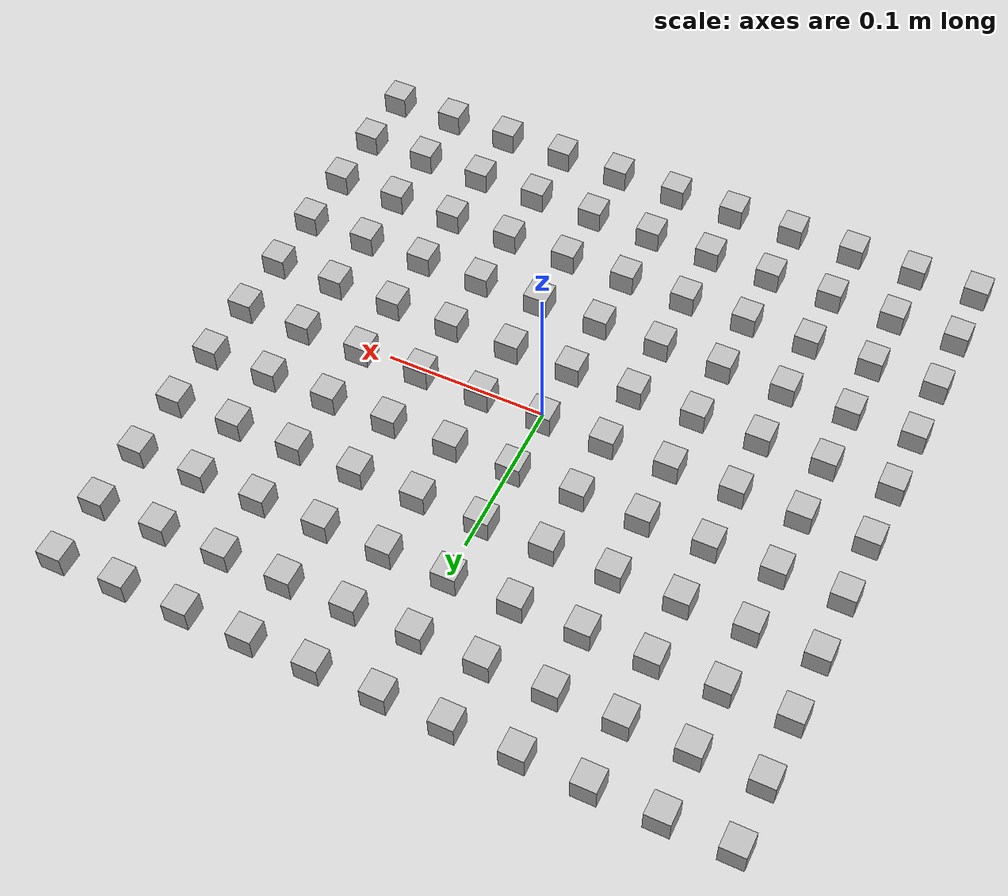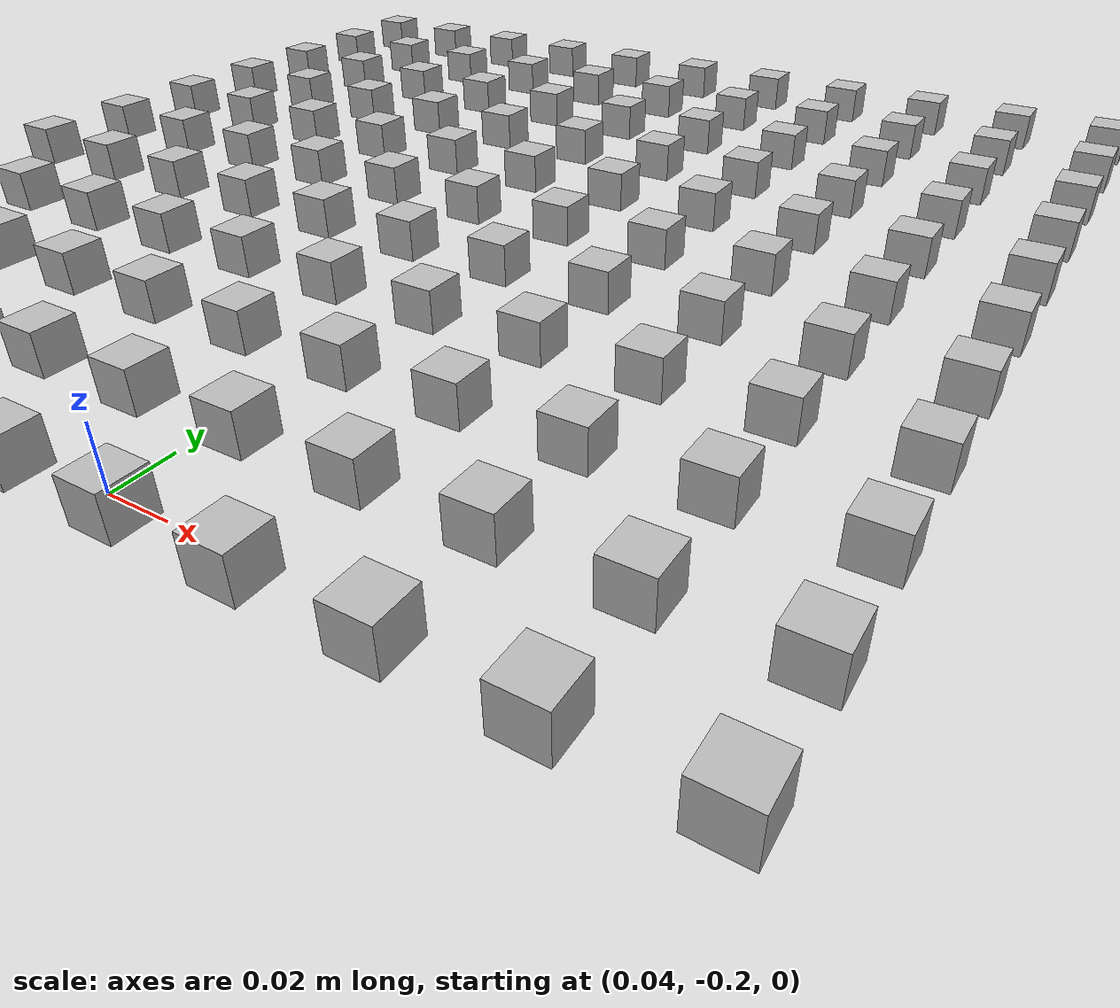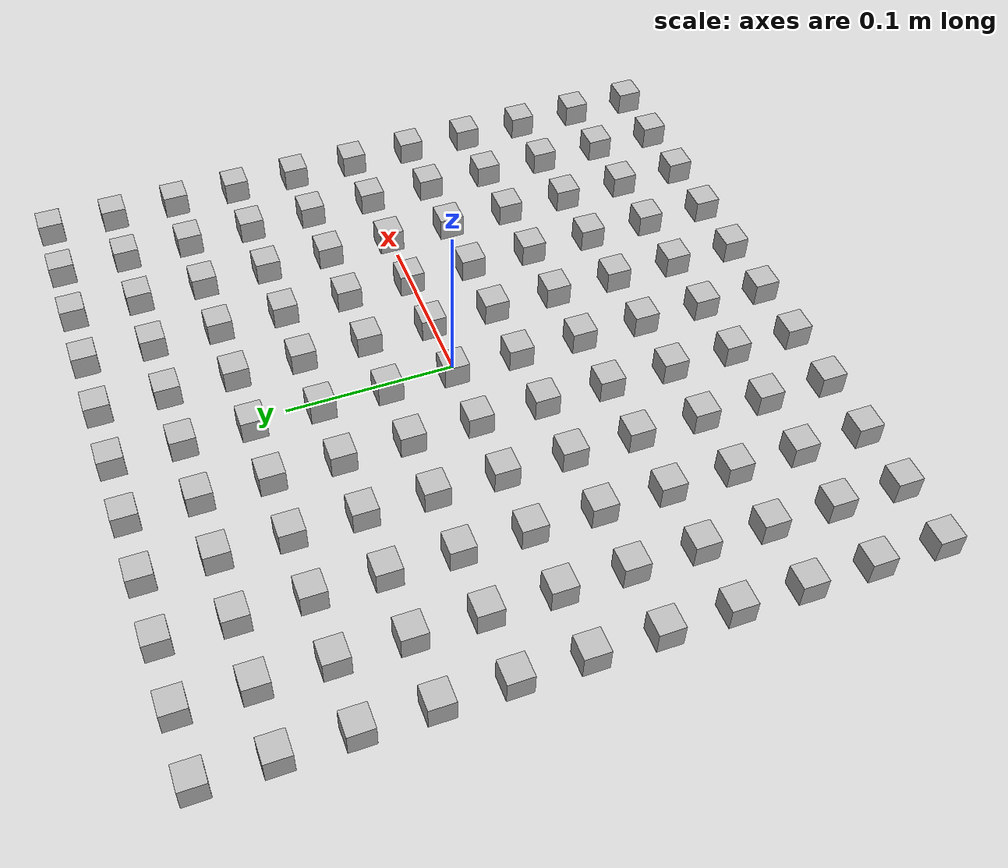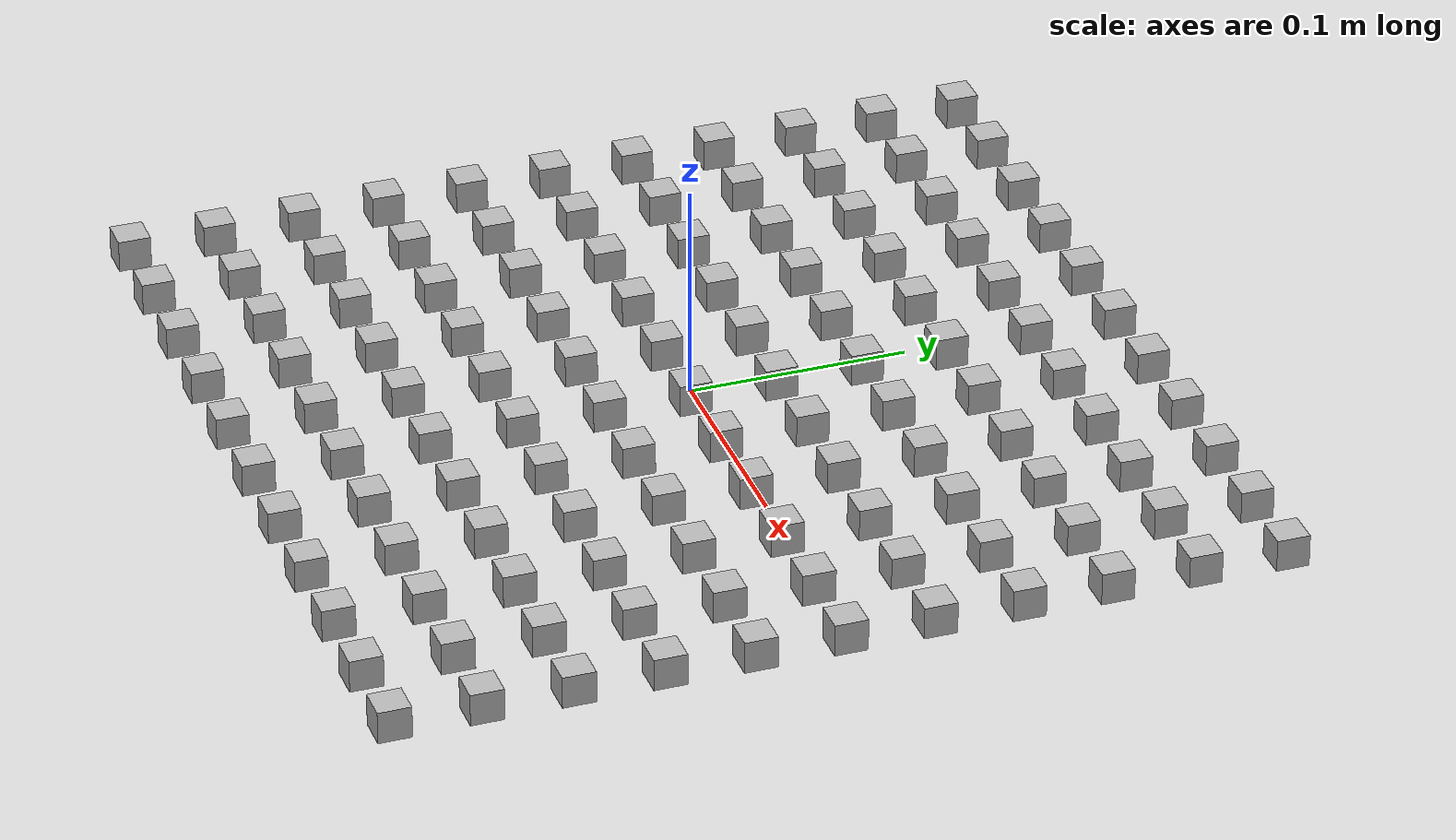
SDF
<sdf version="1.7">
  <model name="mass_mesh_tree">
    <static>false</static>
    <link name="mass_x-5_y-5">
      <pose>-0.2 -0.2 0 0 0 0</pose>
      <inertial>
        <mass>0.0008264462809917356</mass>
        <inertia>
          <ixx>1e-5</ixx>
          <ixy>0</ixy>
          <ixz>0</ixz>
          <iyy>1e-5</iyy>
          <iyz>0</iyz>
          <izz>1e-5</izz>
        </inertia>
      </inertial>
      <collision name="collision_x-5_y-5">
        <geometry>
          <sphere>
            <radius>0.001</radius>
          </sphere>
        </geometry>
      </collision>
      <visual name="visual_x-5_y-5">
        <geometry>
          <box>
            <size>0.015 0.015 0.015</size>
          </box>
        </geometry>
      </visual>
    </link>
    <link name="mass_x-4_y-5">
      <pose>-0.16 -0.2 0 0 0 0</pose>
      <inertial>
        <mass>0.0008264462809917356</mass>
        <inertia>
          <ixx>1e-5</ixx>
          <ixy>0</ixy>
          <ixz>0</ixz>
          <iyy>1e-5</iyy>
          <iyz>0</iyz>
          <izz>1e-5</izz>
        </inertia>
      </inertial>
      <collision name="collision_x-4_y-5">
        <geometry>
          <sphere>
            <radius>0.001</radius>
          </sphere>
        </geometry>
      </collision>
      <visual name="visual_x-4_y-5">
        <geometry>
          <box>
            <size>0.015 0.015 0.015</size>
          </box>
        </geometry>
      </visual>
    </link>
    <link name="mass_x-3_y-5">
      <pose>-0.12 -0.2 0 0 0 0</pose>
      <inertial>
        <mass>0.0008264462809917356</mass>
        <inertia>
          <ixx>1e-5</ixx>
          <ixy>0</ixy>
          <ixz>0</ixz>
          <iyy>1e-5</iyy>
          <iyz>0</iyz>
          <izz>1e-5</izz>
        </inertia>
      </inertial>
      <collision name="collision_x-3_y-5">
        <geometry>
          <sphere>
            <radius>0.001</radius>
          </sphere>
        </geometry>
      </collision>
      <visual name="visual_x-3_y-5">
        <geometry>
          <box>
            <size>0.015 0.015 0.015</size>
          </box>
        </geometry>
      </visual>
    </link>
    <link name="mass_x-2_y-5">
      <pose>-0.08 -0.2 0 0 0 0</pose>
      <inertial>
        <mass>0.0008264462809917356</mass>
        <inertia>
          <ixx>1e-5</ixx>
          <ixy>0</ixy>
          <ixz>0</ixz>
          <iyy>1e-5</iyy>
          <iyz>0</iyz>
          <izz>1e-5</izz>
        </inertia>
      </inertial>
      <collision name="collision_x-2_y-5">
        <geometry>
          <sphere>
            <radius>0.001</radius>
          </sphere>
        </geometry>
      </collision>
      <visual name="visual_x-2_y-5">
        <geometry>
          <box>
            <size>0.015 0.015 0.015</size>
          </box>
        </geometry>
      </visual>
    </link>
    <link name="mass_x-1_y-5">
      <pose>-0.04 -0.2 0 0 0 0</pose>
      <inertial>
        <mass>0.0008264462809917356</mass>
        <inertia>
          <ixx>1e-5</ixx>
          <ixy>0</ixy>
          <ixz>0</ixz>
          <iyy>1e-5</iyy>
          <iyz>0</iyz>
          <izz>1e-5</izz>
        </inertia>
      </inertial>
      <collision name="collision_x-1_y-5">
        <geometry>
          <sphere>
            <radius>0.001</radius>
          </sphere>
        </geometry>
      </collision>
      <visual name="visual_x-1_y-5">
        <geometry>
          <box>
            <size>0.015 0.015 0.015</size>
          </box>
        </geometry>
      </visual>
    </link>
    <link name="mass_x0_y-5">
      <pose>0.0 -0.2 0 0 0 0</pose>
      <inertial>
        <mass>0.0008264462809917356</mass>
        <inertia>
          <ixx>1e-5</ixx>
          <ixy>0</ixy>
          <ixz>0</ixz>
          <iyy>1e-5</iyy>
          <iyz>0</iyz>
          <izz>1e-5</izz>
        </inertia>
      </inertial>
      <collision name="collision_x0_y-5">
        <geometry>
          <sphere>
            <radius>0.001</radius>
          </sphere>
        </geometry>
      </collision>
      <visual name="visual_x0_y-5">
        <geometry>
          <box>
            <size>0.015 0.015 0.015</size>
          </box>
        </geometry>
      </visual>
    </link>
    <link name="mass_x1_y-5">
      <pose>0.04 -0.2 0 0 0 0</pose>
      <inertial>
        <mass>0.0008264462809917356</mass>
        <inertia>
          <ixx>1e-5</ixx>
          <ixy>0</ixy>
          <ixz>0</ixz>
          <iyy>1e-5</iyy>
          <iyz>0</iyz>
          <izz>1e-5</izz>
        </inertia>
      </inertial>
      <collision name="collision_x1_y-5">
        <geometry>
          <sphere>
            <radius>0.001</radius>
          </sphere>
        </geometry>
      </collision>
      <visual name="visual_x1_y-5">
        <geometry>
          <box>
            <size>0.015 0.015 0.015</size>
          </box>
        </geometry>
      </visual>
    </link>
    <link name="mass_x2_y-5">
      <pose>0.08 -0.2 0 0 0 0</pose>
      <inertial>
        <mass>0.0008264462809917356</mass>
        <inertia>
          <ixx>1e-5</ixx>
          <ixy>0</ixy>
          <ixz>0</ixz>
          <iyy>1e-5</iyy>
          <iyz>0</iyz>
          <izz>1e-5</izz>
        </inertia>
      </inertial>
      <collision name="collision_x2_y-5">
        <geometry>
          <sphere>
            <radius>0.001</radius>
          </sphere>
        </geometry>
      </collision>
      <visual name="visual_x2_y-5">
        <geometry>
          <box>
            <size>0.015 0.015 0.015</size>
          </box>
        </geometry>
      </visual>
    </link>
    <link name="mass_x3_y-5">
      <pose>0.12 -0.2 0 0 0 0</pose>
      <inertial>
        <mass>0.0008264462809917356</mass>
        <inertia>
          <ixx>1e-5</ixx>
          <ixy>0</ixy>
          <ixz>0</ixz>
          <iyy>1e-5</iyy>
          <iyz>0</iyz>
          <izz>1e-5</izz>
        </inertia>
      </inertial>
      <collision name="collision_x3_y-5">
        <geometry>
          <sphere>
            <radius>0.001</radius>
          </sphere>
        </geometry>
      </collision>
      <visual name="visual_x3_y-5">
        <geometry>
          <box>
            <size>0.015 0.015 0.015</size>
          </box>
        </geometry>
      </visual>
    </link>
    <link name="mass_x4_y-5">
      <pose>0.16 -0.2 0 0 0 0</pose>
      <inertial>
        <mass>0.0008264462809917356</mass>
        <inertia>
          <ixx>1e-5</ixx>
          <ixy>0</ixy>
          <ixz>0</ixz>
          <iyy>1e-5</iyy>
          <iyz>0</iyz>
          <izz>1e-5</izz>
        </inertia>
      </inertial>
      <collision name="collision_x4_y-5">
        <geometry>
          <sphere>
            <radius>0.001</radius>
          </sphere>
        </geometry>
      </collision>
      <visual name="visual_x4_y-5">
        <geometry>
          <box>
            <size>0.015 0.015 0.015</size>
          </box>
        </geometry>
      </visual>
    </link>
    <link name="mass_x5_y-5">
      <pose>0.2 -0.2 0 0 0 0</pose>
      <inertial>
        <mass>0.0008264462809917356</mass>
        <inertia>
          <ixx>1e-5</ixx>
          <ixy>0</ixy>
          <ixz>0</ixz>
          <iyy>1e-5</iyy>
          <iyz>0</iyz>
          <izz>1e-5</izz>
        </inertia>
      </inertial>
      <collision name="collision_x5_y-5">
        <geometry>
          <sphere>
            <radius>0.001</radius>
          </sphere>
        </geometry>
      </collision>
      <visual name="visual_x5_y-5">
        <geometry>
          <box>
            <size>0.015 0.015 0.015</size>
          </box>
        </geometry>
      </visual>
    </link>
    <link name="mass_x-5_y-4">
      <pose>-0.2 -0.16 0 0 0 0</pose>
      <inertial>
        <mass>0.0008264462809917356</mass>
        <inertia>
          <ixx>1e-5</ixx>
          <ixy>0</ixy>
          <ixz>0</ixz>
          <iyy>1e-5</iyy>
          <iyz>0</iyz>
          <izz>1e-5</izz>
        </inertia>
      </inertial>
      <collision name="collision_x-5_y-4">
        <geometry>
          <sphere>
            <radius>0.001</radius>
          </sphere>
        </geometry>
      </collision>
      <visual name="visual_x-5_y-4">
        <geometry>
          <box>
            <size>0.015 0.015 0.015</size>
          </box>
        </geometry>
      </visual>
    </link>
    <link name="mass_x-4_y-4">
      <pose>-0.16 -0.16 0 0 0 0</pose>
      <inertial>
        <mass>0.0008264462809917356</mass>
        <inertia>
          <ixx>1e-5</ixx>
          <ixy>0</ixy>
          <ixz>0</ixz>
          <iyy>1e-5</iyy>
          <iyz>0</iyz>
          <izz>1e-5</izz>
        </inertia>
      </inertial>
      <collision name="collision_x-4_y-4">
        <geometry>
          <sphere>
            <radius>0.001</radius>
          </sphere>
        </geometry>
      </collision>
      <visual name="visual_x-4_y-4">
        <geometry>
          <box>
            <size>0.015 0.015 0.015</size>
          </box>
        </geometry>
      </visual>
    </link>
    <link name="mass_x-3_y-4">
      <pose>-0.12 -0.16 0 0 0 0</pose>
      <inertial>
        <mass>0.0008264462809917356</mass>
        <inertia>
          <ixx>1e-5</ixx>
          <ixy>0</ixy>
          <ixz>0</ixz>
          <iyy>1e-5</iyy>
          <iyz>0</iyz>
          <izz>1e-5</izz>
        </inertia>
      </inertial>
      <collision name="collision_x-3_y-4">
        <geometry>
          <sphere>
            <radius>0.001</radius>
          </sphere>
        </geometry>
      </collision>
      <visual name="visual_x-3_y-4">
        <geometry>
          <box>
            <size>0.015 0.015 0.015</size>
          </box>
        </geometry>
      </visual>
    </link>
    <link name="mass_x-2_y-4">
      <pose>-0.08 -0.16 0 0 0 0</pose>
      <inertial>
        <mass>0.0008264462809917356</mass>
        <inertia>
          <ixx>1e-5</ixx>
          <ixy>0</ixy>
          <ixz>0</ixz>
          <iyy>1e-5</iyy>
          <iyz>0</iyz>
          <izz>1e-5</izz>
        </inertia>
      </inertial>
      <collision name="collision_x-2_y-4">
        <geometry>
          <sphere>
            <radius>0.001</radius>
          </sphere>
        </geometry>
      </collision>
      <visual name="visual_x-2_y-4">
        <geometry>
          <box>
            <size>0.015 0.015 0.015</size>
          </box>
        </geometry>
      </visual>
    </link>
    <link name="mass_x-1_y-4">
      <pose>-0.04 -0.16 0 0 0 0</pose>
      <inertial>
        <mass>0.0008264462809917356</mass>
        <inertia>
          <ixx>1e-5</ixx>
          <ixy>0</ixy>
          <ixz>0</ixz>
          <iyy>1e-5</iyy>
          <iyz>0</iyz>
          <izz>1e-5</izz>
        </inertia>
      </inertial>
      <collision name="collision_x-1_y-4">
        <geometry>
          <sphere>
            <radius>0.001</radius>
          </sphere>
        </geometry>
      </collision>
      <visual name="visual_x-1_y-4">
        <geometry>
          <box>
            <size>0.015 0.015 0.015</size>
          </box>
        </geometry>
      </visual>
    </link>
    <link name="mass_x0_y-4">
      <pose>0.0 -0.16 0 0 0 0</pose>
      <inertial>
        <mass>0.0008264462809917356</mass>
        <inertia>
          <ixx>1e-5</ixx>
          <ixy>0</ixy>
          <ixz>0</ixz>
          <iyy>1e-5</iyy>
          <iyz>0</iyz>
          <izz>1e-5</izz>
        </inertia>
      </inertial>
      <collision name="collision_x0_y-4">
        <geometry>
          <sphere>
            <radius>0.001</radius>
          </sphere>
        </geometry>
      </collision>
      <visual name="visual_x0_y-4">
        <geometry>
          <box>
            <size>0.015 0.015 0.015</size>
          </box>
        </geometry>
      </visual>
    </link>
    <link name="mass_x1_y-4">
      <pose>0.04 -0.16 0 0 0 0</pose>
      <inertial>
        <mass>0.0008264462809917356</mass>
        <inertia>
          <ixx>1e-5</ixx>
          <ixy>0</ixy>
          <ixz>0</ixz>
          <iyy>1e-5</iyy>
          <iyz>0</iyz>
          <izz>1e-5</izz>
        </inertia>
      </inertial>
      <collision name="collision_x1_y-4">
        <geometry>
          <sphere>
            <radius>0.001</radius>
          </sphere>
        </geometry>
      </collision>
      <visual name="visual_x1_y-4">
        <geometry>
          <box>
            <size>0.015 0.015 0.015</size>
          </box>
        </geometry>
      </visual>
    </link>
    <link name="mass_x2_y-4">
      <pose>0.08 -0.16 0 0 0 0</pose>
      <inertial>
        <mass>0.0008264462809917356</mass>
        <inertia>
          <ixx>1e-5</ixx>
          <ixy>0</ixy>
          <ixz>0</ixz>
          <iyy>1e-5</iyy>
          <iyz>0</iyz>
          <izz>1e-5</izz>
        </inertia>
      </inertial>
      <collision name="collision_x2_y-4">
        <geometry>
          <sphere>
            <radius>0.001</radius>
          </sphere>
        </geometry>
      </collision>
      <visual name="visual_x2_y-4">
        <geometry>
          <box>
            <size>0.015 0.015 0.015</size>
          </box>
        </geometry>
      </visual>
    </link>
    <link name="mass_x3_y-4">
      <pose>0.12 -0.16 0 0 0 0</pose>
      <inertial>
        <mass>0.0008264462809917356</mass>
        <inertia>
          <ixx>1e-5</ixx>
          <ixy>0</ixy>
          <ixz>0</ixz>
          <iyy>1e-5</iyy>
          <iyz>0</iyz>
          <izz>1e-5</izz>
        </inertia>
      </inertial>
      <collision name="collision_x3_y-4">
        <geometry>
          <sphere>
            <radius>0.001</radius>
          </sphere>
        </geometry>
      </collision>
      <visual name="visual_x3_y-4">
        <geometry>
          <box>
            <size>0.015 0.015 0.015</size>
          </box>
        </geometry>
      </visual>
    </link>
    <link name="mass_x4_y-4">
      <pose>0.16 -0.16 0 0 0 0</pose>
      <inertial>
        <mass>0.0008264462809917356</mass>
        <inertia>
          <ixx>1e-5</ixx>
          <ixy>0</ixy>
          <ixz>0</ixz>
          <iyy>1e-5</iyy>
          <iyz>0</iyz>
          <izz>1e-5</izz>
        </inertia>
      </inertial>
      <collision name="collision_x4_y-4">
        <geometry>
          <sphere>
            <radius>0.001</radius>
          </sphere>
        </geometry>
      </collision>
      <visual name="visual_x4_y-4">
        <geometry>
          <box>
            <size>0.015 0.015 0.015</size>
          </box>
        </geometry>
      </visual>
    </link>
    <link name="mass_x5_y-4">
      <pose>0.2 -0.16 0 0 0 0</pose>
      <inertial>
        <mass>0.0008264462809917356</mass>
        <inertia>
          <ixx>1e-5</ixx>
          <ixy>0</ixy>
          <ixz>0</ixz>
          <iyy>1e-5</iyy>
          <iyz>0</iyz>
          <izz>1e-5</izz>
        </inertia>
      </inertial>
      <collision name="collision_x5_y-4">
        <geometry>
          <sphere>
            <radius>0.001</radius>
          </sphere>
        </geometry>
      </collision>
      <visual name="visual_x5_y-4">
        <geometry>
          <box>
            <size>0.015 0.015 0.015</size>
          </box>
        </geometry>
      </visual>
    </link>
    <link name="mass_x-5_y-3">
      <pose>-0.2 -0.12 0 0 0 0</pose>
      <inertial>
        <mass>0.0008264462809917356</mass>
        <inertia>
          <ixx>1e-5</ixx>
          <ixy>0</ixy>
          <ixz>0</ixz>
          <iyy>1e-5</iyy>
          <iyz>0</iyz>
          <izz>1e-5</izz>
        </inertia>
      </inertial>
      <collision name="collision_x-5_y-3">
        <geometry>
          <sphere>
            <radius>0.001</radius>
          </sphere>
        </geometry>
      </collision>
      <visual name="visual_x-5_y-3">
        <geometry>
          <box>
            <size>0.015 0.015 0.015</size>
          </box>
        </geometry>
      </visual>
    </link>
    <link name="mass_x-4_y-3">
      <pose>-0.16 -0.12 0 0 0 0</pose>
      <inertial>
        <mass>0.0008264462809917356</mass>
        <inertia>
          <ixx>1e-5</ixx>
          <ixy>0</ixy>
          <ixz>0</ixz>
          <iyy>1e-5</iyy>
          <iyz>0</iyz>
          <izz>1e-5</izz>
        </inertia>
      </inertial>
      <collision name="collision_x-4_y-3">
        <geometry>
          <sphere>
            <radius>0.001</radius>
          </sphere>
        </geometry>
      </collision>
      <visual name="visual_x-4_y-3">
        <geometry>
          <box>
            <size>0.015 0.015 0.015</size>
          </box>
        </geometry>
      </visual>
    </link>
    <link name="mass_x-3_y-3">
      <pose>-0.12 -0.12 0 0 0 0</pose>
      <inertial>
        <mass>0.0008264462809917356</mass>
        <inertia>
          <ixx>1e-5</ixx>
          <ixy>0</ixy>
          <ixz>0</ixz>
          <iyy>1e-5</iyy>
          <iyz>0</iyz>
          <izz>1e-5</izz>
        </inertia>
      </inertial>
      <collision name="collision_x-3_y-3">
        <geometry>
          <sphere>
            <radius>0.001</radius>
          </sphere>
        </geometry>
      </collision>
      <visual name="visual_x-3_y-3">
        <geometry>
          <box>
            <size>0.015 0.015 0.015</size>
          </box>
        </geometry>
      </visual>
    </link>
    <link name="mass_x-2_y-3">
      <pose>-0.08 -0.12 0 0 0 0</pose>
      <inertial>
        <mass>0.0008264462809917356</mass>
        <inertia>
          <ixx>1e-5</ixx>
          <ixy>0</ixy>
          <ixz>0</ixz>
          <iyy>1e-5</iyy>
          <iyz>0</iyz>
          <izz>1e-5</izz>
        </inertia>
      </inertial>
      <collision name="collision_x-2_y-3">
        <geometry>
          <sphere>
            <radius>0.001</radius>
          </sphere>
        </geometry>
      </collision>
      <visual name="visual_x-2_y-3">
        <geometry>
          <box>
            <size>0.015 0.015 0.015</size>
          </box>
        </geometry>
      </visual>
    </link>
    <link name="mass_x-1_y-3">
      <pose>-0.04 -0.12 0 0 0 0</pose>
      <inertial>
        <mass>0.0008264462809917356</mass>
        <inertia>
          <ixx>1e-5</ixx>
          <ixy>0</ixy>
          <ixz>0</ixz>
          <iyy>1e-5</iyy>
          <iyz>0</iyz>
          <izz>1e-5</izz>
        </inertia>
      </inertial>
      <collision name="collision_x-1_y-3">
        <geometry>
          <sphere>
            <radius>0.001</radius>
          </sphere>
        </geometry>
      </collision>
      <visual name="visual_x-1_y-3">
        <geometry>
          <box>
            <size>0.015 0.015 0.015</size>
          </box>
        </geometry>
      </visual>
    </link>
    <link name="mass_x0_y-3">
      <pose>0.0 -0.12 0 0 0 0</pose>
      <inertial>
        <mass>0.0008264462809917356</mass>
        <inertia>
          <ixx>1e-5</ixx>
          <ixy>0</ixy>
          <ixz>0</ixz>
          <iyy>1e-5</iyy>
          <iyz>0</iyz>
          <izz>1e-5</izz>
        </inertia>
      </inertial>
      <collision name="collision_x0_y-3">
        <geometry>
          <sphere>
            <radius>0.001</radius>
          </sphere>
        </geometry>
      </collision>
      <visual name="visual_x0_y-3">
        <geometry>
          <box>
            <size>0.015 0.015 0.015</size>
          </box>
        </geometry>
      </visual>
    </link>
    <link name="mass_x1_y-3">
      <pose>0.04 -0.12 0 0 0 0</pose>
      <inertial>
        <mass>0.0008264462809917356</mass>
        <inertia>
          <ixx>1e-5</ixx>
          <ixy>0</ixy>
          <ixz>0</ixz>
          <iyy>1e-5</iyy>
          <iyz>0</iyz>
          <izz>1e-5</izz>
        </inertia>
      </inertial>
      <collision name="collision_x1_y-3">
        <geometry>
          <sphere>
            <radius>0.001</radius>
          </sphere>
        </geometry>
      </collision>
      <visual name="visual_x1_y-3">
        <geometry>
          <box>
            <size>0.015 0.015 0.015</size>
          </box>
        </geometry>
      </visual>
    </link>
    <link name="mass_x2_y-3">
      <pose>0.08 -0.12 0 0 0 0</pose>
      <inertial>
        <mass>0.0008264462809917356</mass>
        <inertia>
          <ixx>1e-5</ixx>
          <ixy>0</ixy>
          <ixz>0</ixz>
          <iyy>1e-5</iyy>
          <iyz>0</iyz>
          <izz>1e-5</izz>
        </inertia>
      </inertial>
      <collision name="collision_x2_y-3">
        <geometry>
          <sphere>
            <radius>0.001</radius>
          </sphere>
        </geometry>
      </collision>
      <visual name="visual_x2_y-3">
        <geometry>
          <box>
            <size>0.015 0.015 0.015</size>
          </box>
        </geometry>
      </visual>
    </link>
    <link name="mass_x3_y-3">
      <pose>0.12 -0.12 0 0 0 0</pose>
      <inertial>
        <mass>0.0008264462809917356</mass>
        <inertia>
          <ixx>1e-5</ixx>
          <ixy>0</ixy>
          <ixz>0</ixz>
          <iyy>1e-5</iyy>
          <iyz>0</iyz>
          <izz>1e-5</izz>
        </inertia>
      </inertial>
      <collision name="collision_x3_y-3">
        <geometry>
          <sphere>
            <radius>0.001</radius>
          </sphere>
        </geometry>
      </collision>
      <visual name="visual_x3_y-3">
        <geometry>
          <box>
            <size>0.015 0.015 0.015</size>
          </box>
        </geometry>
      </visual>
    </link>
    <link name="mass_x4_y-3">
      <pose>0.16 -0.12 0 0 0 0</pose>
      <inertial>
        <mass>0.0008264462809917356</mass>
        <inertia>
          <ixx>1e-5</ixx>
          <ixy>0</ixy>
          <ixz>0</ixz>
          <iyy>1e-5</iyy>
          <iyz>0</iyz>
          <izz>1e-5</izz>
        </inertia>
      </inertial>
      <collision name="collision_x4_y-3">
        <geometry>
          <sphere>
            <radius>0.001</radius>
          </sphere>
        </geometry>
      </collision>
      <visual name="visual_x4_y-3">
        <geometry>
          <box>
            <size>0.015 0.015 0.015</size>
          </box>
        </geometry>
      </visual>
    </link>
    <link name="mass_x5_y-3">
      <pose>0.2 -0.12 0 0 0 0</pose>
      <inertial>
        <mass>0.0008264462809917356</mass>
        <inertia>
          <ixx>1e-5</ixx>
          <ixy>0</ixy>
          <ixz>0</ixz>
          <iyy>1e-5</iyy>
          <iyz>0</iyz>
          <izz>1e-5</izz>
        </inertia>
      </inertial>
      <collision name="collision_x5_y-3">
        <geometry>
          <sphere>
            <radius>0.001</radius>
          </sphere>
        </geometry>
      </collision>
      <visual name="visual_x5_y-3">
        <geometry>
          <box>
            <size>0.015 0.015 0.015</size>
          </box>
        </geometry>
      </visual>
    </link>
    <link name="mass_x-5_y-2">
      <pose>-0.2 -0.08 0 0 0 0</pose>
      <inertial>
        <mass>0.0008264462809917356</mass>
        <inertia>
          <ixx>1e-5</ixx>
          <ixy>0</ixy>
          <ixz>0</ixz>
          <iyy>1e-5</iyy>
          <iyz>0</iyz>
          <izz>1e-5</izz>
        </inertia>
      </inertial>
      <collision name="collision_x-5_y-2">
        <geometry>
          <sphere>
            <radius>0.001</radius>
          </sphere>
        </geometry>
      </collision>
      <visual name="visual_x-5_y-2">
        <geometry>
          <box>
            <size>0.015 0.015 0.015</size>
          </box>
        </geometry>
      </visual>
    </link>
    <link name="mass_x-4_y-2">
      <pose>-0.16 -0.08 0 0 0 0</pose>
      <inertial>
        <mass>0.0008264462809917356</mass>
        <inertia>
          <ixx>1e-5</ixx>
          <ixy>0</ixy>
          <ixz>0</ixz>
          <iyy>1e-5</iyy>
          <iyz>0</iyz>
          <izz>1e-5</izz>
        </inertia>
      </inertial>
      <collision name="collision_x-4_y-2">
        <geometry>
          <sphere>
            <radius>0.001</radius>
          </sphere>
        </geometry>
      </collision>
      <visual name="visual_x-4_y-2">
        <geometry>
          <box>
            <size>0.015 0.015 0.015</size>
          </box>
        </geometry>
      </visual>
    </link>
    <link name="mass_x-3_y-2">
      <pose>-0.12 -0.08 0 0 0 0</pose>
      <inertial>
        <mass>0.0008264462809917356</mass>
        <inertia>
          <ixx>1e-5</ixx>
          <ixy>0</ixy>
          <ixz>0</ixz>
          <iyy>1e-5</iyy>
          <iyz>0</iyz>
          <izz>1e-5</izz>
        </inertia>
      </inertial>
      <collision name="collision_x-3_y-2">
        <geometry>
          <sphere>
            <radius>0.001</radius>
          </sphere>
        </geometry>
      </collision>
      <visual name="visual_x-3_y-2">
        <geometry>
          <box>
            <size>0.015 0.015 0.015</size>
          </box>
        </geometry>
      </visual>
    </link>
    <link name="mass_x-2_y-2">
      <pose>-0.08 -0.08 0 0 0 0</pose>
      <inertial>
        <mass>0.0008264462809917356</mass>
        <inertia>
          <ixx>1e-5</ixx>
          <ixy>0</ixy>
          <ixz>0</ixz>
          <iyy>1e-5</iyy>
          <iyz>0</iyz>
          <izz>1e-5</izz>
        </inertia>
      </inertial>
      <collision name="collision_x-2_y-2">
        <geometry>
          <sphere>
            <radius>0.001</radius>
          </sphere>
        </geometry>
      </collision>
      <visual name="visual_x-2_y-2">
        <geometry>
          <box>
            <size>0.015 0.015 0.015</size>
          </box>
        </geometry>
      </visual>
    </link>
    <link name="mass_x-1_y-2">
      <pose>-0.04 -0.08 0 0 0 0</pose>
      <inertial>
        <mass>0.0008264462809917356</mass>
        <inertia>
          <ixx>1e-5</ixx>
          <ixy>0</ixy>
          <ixz>0</ixz>
          <iyy>1e-5</iyy>
          <iyz>0</iyz>
          <izz>1e-5</izz>
        </inertia>
      </inertial>
      <collision name="collision_x-1_y-2">
        <geometry>
          <sphere>
            <radius>0.001</radius>
          </sphere>
        </geometry>
      </collision>
      <visual name="visual_x-1_y-2">
        <geometry>
          <box>
            <size>0.015 0.015 0.015</size>
          </box>
        </geometry>
      </visual>
    </link>
    <link name="mass_x0_y-2">
      <pose>0.0 -0.08 0 0 0 0</pose>
      <inertial>
        <mass>0.0008264462809917356</mass>
        <inertia>
          <ixx>1e-5</ixx>
          <ixy>0</ixy>
          <ixz>0</ixz>
          <iyy>1e-5</iyy>
          <iyz>0</iyz>
          <izz>1e-5</izz>
        </inertia>
      </inertial>
      <collision name="collision_x0_y-2">
        <geometry>
          <sphere>
            <radius>0.001</radius>
          </sphere>
        </geometry>
      </collision>
      <visual name="visual_x0_y-2">
        <geometry>
          <box>
            <size>0.015 0.015 0.015</size>
          </box>
        </geometry>
      </visual>
    </link>
    <link name="mass_x1_y-2">
      <pose>0.04 -0.08 0 0 0 0</pose>
      <inertial>
        <mass>0.0008264462809917356</mass>
        <inertia>
          <ixx>1e-5</ixx>
          <ixy>0</ixy>
          <ixz>0</ixz>
          <iyy>1e-5</iyy>
          <iyz>0</iyz>
          <izz>1e-5</izz>
        </inertia>
      </inertial>
      <collision name="collision_x1_y-2">
        <geometry>
          <sphere>
            <radius>0.001</radius>
          </sphere>
        </geometry>
      </collision>
      <visual name="visual_x1_y-2">
        <geometry>
          <box>
            <size>0.015 0.015 0.015</size>
          </box>
        </geometry>
      </visual>
    </link>
    <link name="mass_x2_y-2">
      <pose>0.08 -0.08 0 0 0 0</pose>
      <inertial>
        <mass>0.0008264462809917356</mass>
        <inertia>
          <ixx>1e-5</ixx>
          <ixy>0</ixy>
          <ixz>0</ixz>
          <iyy>1e-5</iyy>
          <iyz>0</iyz>
          <izz>1e-5</izz>
        </inertia>
      </inertial>
      <collision name="collision_x2_y-2">
        <geometry>
          <sphere>
            <radius>0.001</radius>
          </sphere>
        </geometry>
      </collision>
      <visual name="visual_x2_y-2">
        <geometry>
          <box>
            <size>0.015 0.015 0.015</size>
          </box>
        </geometry>
      </visual>
    </link>
    <link name="mass_x3_y-2">
      <pose>0.12 -0.08 0 0 0 0</pose>
      <inertial>
        <mass>0.0008264462809917356</mass>
        <inertia>
          <ixx>1e-5</ixx>
          <ixy>0</ixy>
          <ixz>0</ixz>
          <iyy>1e-5</iyy>
          <iyz>0</iyz>
          <izz>1e-5</izz>
        </inertia>
      </inertial>
      <collision name="collision_x3_y-2">
        <geometry>
          <sphere>
            <radius>0.001</radius>
          </sphere>
        </geometry>
      </collision>
      <visual name="visual_x3_y-2">
        <geometry>
          <box>
            <size>0.015 0.015 0.015</size>
          </box>
        </geometry>
      </visual>
    </link>
    <link name="mass_x4_y-2">
      <pose>0.16 -0.08 0 0 0 0</pose>
      <inertial>
        <mass>0.0008264462809917356</mass>
        <inertia>
          <ixx>1e-5</ixx>
          <ixy>0</ixy>
          <ixz>0</ixz>
          <iyy>1e-5</iyy>
          <iyz>0</iyz>
          <izz>1e-5</izz>
        </inertia>
      </inertial>
      <collision name="collision_x4_y-2">
        <geometry>
          <sphere>
            <radius>0.001</radius>
          </sphere>
        </geometry>
      </collision>
      <visual name="visual_x4_y-2">
        <geometry>
          <box>
            <size>0.015 0.015 0.015</size>
          </box>
        </geometry>
      </visual>
    </link>
    <link name="mass_x5_y-2">
      <pose>0.2 -0.08 0 0 0 0</pose>
      <inertial>
        <mass>0.0008264462809917356</mass>
        <inertia>
          <ixx>1e-5</ixx>
          <ixy>0</ixy>
          <ixz>0</ixz>
          <iyy>1e-5</iyy>
          <iyz>0</iyz>
          <izz>1e-5</izz>
        </inertia>
      </inertial>
      <collision name="collision_x5_y-2">
        <geometry>
          <sphere>
            <radius>0.001</radius>
          </sphere>
        </geometry>
      </collision>
      <visual name="visual_x5_y-2">
        <geometry>
          <box>
            <size>0.015 0.015 0.015</size>
          </box>
        </geometry>
      </visual>
    </link>
    <link name="mass_x-5_y-1">
      <pose>-0.2 -0.04 0 0 0 0</pose>
      <inertial>
        <mass>0.0008264462809917356</mass>
        <inertia>
          <ixx>1e-5</ixx>
          <ixy>0</ixy>
          <ixz>0</ixz>
          <iyy>1e-5</iyy>
          <iyz>0</iyz>
          <izz>1e-5</izz>
        </inertia>
      </inertial>
      <collision name="collision_x-5_y-1">
        <geometry>
          <sphere>
            <radius>0.001</radius>
          </sphere>
        </geometry>
      </collision>
      <visual name="visual_x-5_y-1">
        <geometry>
          <box>
            <size>0.015 0.015 0.015</size>
          </box>
        </geometry>
      </visual>
    </link>
    <link name="mass_x-4_y-1">
      <pose>-0.16 -0.04 0 0 0 0</pose>
      <inertial>
        <mass>0.0008264462809917356</mass>
        <inertia>
          <ixx>1e-5</ixx>
          <ixy>0</ixy>
          <ixz>0</ixz>
          <iyy>1e-5</iyy>
          <iyz>0</iyz>
          <izz>1e-5</izz>
        </inertia>
      </inertial>
      <collision name="collision_x-4_y-1">
        <geometry>
          <sphere>
            <radius>0.001</radius>
          </sphere>
        </geometry>
      </collision>
      <visual name="visual_x-4_y-1">
        <geometry>
          <box>
            <size>0.015 0.015 0.015</size>
          </box>
        </geometry>
      </visual>
    </link>
    <link name="mass_x-3_y-1">
      <pose>-0.12 -0.04 0 0 0 0</pose>
      <inertial>
        <mass>0.0008264462809917356</mass>
        <inertia>
          <ixx>1e-5</ixx>
          <ixy>0</ixy>
          <ixz>0</ixz>
          <iyy>1e-5</iyy>
          <iyz>0</iyz>
          <izz>1e-5</izz>
        </inertia>
      </inertial>
      <collision name="collision_x-3_y-1">
        <geometry>
          <sphere>
            <radius>0.001</radius>
          </sphere>
        </geometry>
      </collision>
      <visual name="visual_x-3_y-1">
        <geometry>
          <box>
            <size>0.015 0.015 0.015</size>
          </box>
        </geometry>
      </visual>
    </link>
    <link name="mass_x-2_y-1">
      <pose>-0.08 -0.04 0 0 0 0</pose>
      <inertial>
        <mass>0.0008264462809917356</mass>
        <inertia>
          <ixx>1e-5</ixx>
          <ixy>0</ixy>
          <ixz>0</ixz>
          <iyy>1e-5</iyy>
          <iyz>0</iyz>
          <izz>1e-5</izz>
        </inertia>
      </inertial>
      <collision name="collision_x-2_y-1">
        <geometry>
          <sphere>
            <radius>0.001</radius>
          </sphere>
        </geometry>
      </collision>
      <visual name="visual_x-2_y-1">
        <geometry>
          <box>
            <size>0.015 0.015 0.015</size>
          </box>
        </geometry>
      </visual>
    </link>
    <link name="mass_x-1_y-1">
      <pose>-0.04 -0.04 0 0 0 0</pose>
      <inertial>
        <mass>0.0008264462809917356</mass>
        <inertia>
          <ixx>1e-5</ixx>
          <ixy>0</ixy>
          <ixz>0</ixz>
          <iyy>1e-5</iyy>
          <iyz>0</iyz>
          <izz>1e-5</izz>
        </inertia>
      </inertial>
      <collision name="collision_x-1_y-1">
        <geometry>
          <sphere>
            <radius>0.001</radius>
          </sphere>
        </geometry>
      </collision>
      <visual name="visual_x-1_y-1">
        <geometry>
          <box>
            <size>0.015 0.015 0.015</size>
          </box>
        </geometry>
      </visual>
    </link>
    <link name="mass_x0_y-1">
      <pose>0.0 -0.04 0 0 0 0</pose>
      <inertial>
        <mass>0.0008264462809917356</mass>
        <inertia>
          <ixx>1e-5</ixx>
          <ixy>0</ixy>
          <ixz>0</ixz>
          <iyy>1e-5</iyy>
          <iyz>0</iyz>
          <izz>1e-5</izz>
        </inertia>
      </inertial>
      <collision name="collision_x0_y-1">
        <geometry>
          <sphere>
            <radius>0.001</radius>
          </sphere>
        </geometry>
      </collision>
      <visual name="visual_x0_y-1">
        <geometry>
          <box>
            <size>0.015 0.015 0.015</size>
          </box>
        </geometry>
      </visual>
    </link>
    <link name="mass_x1_y-1">
      <pose>0.04 -0.04 0 0 0 0</pose>
      <inertial>
        <mass>0.0008264462809917356</mass>
        <inertia>
          <ixx>1e-5</ixx>
          <ixy>0</ixy>
          <ixz>0</ixz>
          <iyy>1e-5</iyy>
          <iyz>0</iyz>
          <izz>1e-5</izz>
        </inertia>
      </inertial>
      <collision name="collision_x1_y-1">
        <geometry>
          <sphere>
            <radius>0.001</radius>
          </sphere>
        </geometry>
      </collision>
      <visual name="visual_x1_y-1">
        <geometry>
          <box>
            <size>0.015 0.015 0.015</size>
          </box>
        </geometry>
      </visual>
    </link>
    <link name="mass_x2_y-1">
      <pose>0.08 -0.04 0 0 0 0</pose>
      <inertial>
        <mass>0.0008264462809917356</mass>
        <inertia>
          <ixx>1e-5</ixx>
          <ixy>0</ixy>
          <ixz>0</ixz>
          <iyy>1e-5</iyy>
          <iyz>0</iyz>
          <izz>1e-5</izz>
        </inertia>
      </inertial>
      <collision name="collision_x2_y-1">
        <geometry>
          <sphere>
            <radius>0.001</radius>
          </sphere>
        </geometry>
      </collision>
      <visual name="visual_x2_y-1">
        <geometry>
          <box>
            <size>0.015 0.015 0.015</size>
          </box>
        </geometry>
      </visual>
    </link>
    <link name="mass_x3_y-1">
      <pose>0.12 -0.04 0 0 0 0</pose>
      <inertial>
        <mass>0.0008264462809917356</mass>
        <inertia>
          <ixx>1e-5</ixx>
          <ixy>0</ixy>
          <ixz>0</ixz>
          <iyy>1e-5</iyy>
          <iyz>0</iyz>
          <izz>1e-5</izz>
        </inertia>
      </inertial>
      <collision name="collision_x3_y-1">
        <geometry>
          <sphere>
            <radius>0.001</radius>
          </sphere>
        </geometry>
      </collision>
      <visual name="visual_x3_y-1">
        <geometry>
          <box>
            <size>0.015 0.015 0.015</size>
          </box>
        </geometry>
      </visual>
    </link>
    <link name="mass_x4_y-1">
      <pose>0.16 -0.04 0 0 0 0</pose>
      <inertial>
        <mass>0.0008264462809917356</mass>
        <inertia>
          <ixx>1e-5</ixx>
          <ixy>0</ixy>
          <ixz>0</ixz>
          <iyy>1e-5</iyy>
          <iyz>0</iyz>
          <izz>1e-5</izz>
        </inertia>
      </inertial>
      <collision name="collision_x4_y-1">
        <geometry>
          <sphere>
            <radius>0.001</radius>
          </sphere>
        </geometry>
      </collision>
      <visual name="visual_x4_y-1">
        <geometry>
          <box>
            <size>0.015 0.015 0.015</size>
          </box>
        </geometry>
      </visual>
    </link>
    <link name="mass_x5_y-1">
      <pose>0.2 -0.04 0 0 0 0</pose>
      <inertial>
        <mass>0.0008264462809917356</mass>
        <inertia>
          <ixx>1e-5</ixx>
          <ixy>0</ixy>
          <ixz>0</ixz>
          <iyy>1e-5</iyy>
          <iyz>0</iyz>
          <izz>1e-5</izz>
        </inertia>
      </inertial>
      <collision name="collision_x5_y-1">
        <geometry>
          <sphere>
            <radius>0.001</radius>
          </sphere>
        </geometry>
      </collision>
      <visual name="visual_x5_y-1">
        <geometry>
          <box>
            <size>0.015 0.015 0.015</size>
          </box>
        </geometry>
      </visual>
    </link>
    <link name="mass_x-5_y0">
      <pose>-0.2 0.0 0 0 0 0</pose>
      <inertial>
        <mass>0.0008264462809917356</mass>
        <inertia>
          <ixx>1e-5</ixx>
          <ixy>0</ixy>
          <ixz>0</ixz>
          <iyy>1e-5</iyy>
          <iyz>0</iyz>
          <izz>1e-5</izz>
        </inertia>
      </inertial>
      <collision name="collision_x-5_y0">
        <geometry>
          <sphere>
            <radius>0.001</radius>
          </sphere>
        </geometry>
      </collision>
      <visual name="visual_x-5_y0">
        <geometry>
          <box>
            <size>0.015 0.015 0.015</size>
          </box>
        </geometry>
      </visual>
    </link>
    <link name="mass_x-4_y0">
      <pose>-0.16 0.0 0 0 0 0</pose>
      <inertial>
        <mass>0.0008264462809917356</mass>
        <inertia>
          <ixx>1e-5</ixx>
          <ixy>0</ixy>
          <ixz>0</ixz>
          <iyy>1e-5</iyy>
          <iyz>0</iyz>
          <izz>1e-5</izz>
        </inertia>
      </inertial>
      <collision name="collision_x-4_y0">
        <geometry>
          <sphere>
            <radius>0.001</radius>
          </sphere>
        </geometry>
      </collision>
      <visual name="visual_x-4_y0">
        <geometry>
          <box>
            <size>0.015 0.015 0.015</size>
          </box>
        </geometry>
      </visual>
    </link>
    <link name="mass_x-3_y0">
      <pose>-0.12 0.0 0 0 0 0</pose>
      <inertial>
        <mass>0.0008264462809917356</mass>
        <inertia>
          <ixx>1e-5</ixx>
          <ixy>0</ixy>
          <ixz>0</ixz>
          <iyy>1e-5</iyy>
          <iyz>0</iyz>
          <izz>1e-5</izz>
        </inertia>
      </inertial>
      <collision name="collision_x-3_y0">
        <geometry>
          <sphere>
            <radius>0.001</radius>
          </sphere>
        </geometry>
      </collision>
      <visual name="visual_x-3_y0">
        <geometry>
          <box>
            <size>0.015 0.015 0.015</size>
          </box>
        </geometry>
      </visual>
    </link>
    <link name="mass_x-2_y0">
      <pose>-0.08 0.0 0 0 0 0</pose>
      <inertial>
        <mass>0.0008264462809917356</mass>
        <inertia>
          <ixx>1e-5</ixx>
          <ixy>0</ixy>
          <ixz>0</ixz>
          <iyy>1e-5</iyy>
          <iyz>0</iyz>
          <izz>1e-5</izz>
        </inertia>
      </inertial>
      <collision name="collision_x-2_y0">
        <geometry>
          <sphere>
            <radius>0.001</radius>
          </sphere>
        </geometry>
      </collision>
      <visual name="visual_x-2_y0">
        <geometry>
          <box>
            <size>0.015 0.015 0.015</size>
          </box>
        </geometry>
      </visual>
    </link>
    <link name="mass_x-1_y0">
      <pose>-0.04 0.0 0 0 0 0</pose>
      <inertial>
        <mass>0.0008264462809917356</mass>
        <inertia>
          <ixx>1e-5</ixx>
          <ixy>0</ixy>
          <ixz>0</ixz>
          <iyy>1e-5</iyy>
          <iyz>0</iyz>
          <izz>1e-5</izz>
        </inertia>
      </inertial>
      <collision name="collision_x-1_y0">
        <geometry>
          <sphere>
            <radius>0.001</radius>
          </sphere>
        </geometry>
      </collision>
      <visual name="visual_x-1_y0">
        <geometry>
          <box>
            <size>0.015 0.015 0.015</size>
          </box>
        </geometry>
      </visual>
    </link>
    <link name="mass_x0_y0">
      <pose>0.0 0.0 0 0 0 0</pose>
      <inertial>
        <mass>0.0008264462809917356</mass>
        <inertia>
          <ixx>1e-5</ixx>
          <ixy>0</ixy>
          <ixz>0</ixz>
          <iyy>1e-5</iyy>
          <iyz>0</iyz>
          <izz>1e-5</izz>
        </inertia>
      </inertial>
      <collision name="collision_x0_y0">
        <geometry>
          <sphere>
            <radius>0.001</radius>
          </sphere>
        </geometry>
      </collision>
      <visual name="visual_x0_y0">
        <geometry>
          <box>
            <size>0.015 0.015 0.015</size>
          </box>
        </geometry>
      </visual>
    </link>
    <link name="mass_x1_y0">
      <pose>0.04 0.0 0 0 0 0</pose>
      <inertial>
        <mass>0.0008264462809917356</mass>
        <inertia>
          <ixx>1e-5</ixx>
          <ixy>0</ixy>
          <ixz>0</ixz>
          <iyy>1e-5</iyy>
          <iyz>0</iyz>
          <izz>1e-5</izz>
        </inertia>
      </inertial>
      <collision name="collision_x1_y0">
        <geometry>
          <sphere>
            <radius>0.001</radius>
          </sphere>
        </geometry>
      </collision>
      <visual name="visual_x1_y0">
        <geometry>
          <box>
            <size>0.015 0.015 0.015</size>
          </box>
        </geometry>
      </visual>
    </link>
    <link name="mass_x2_y0">
      <pose>0.08 0.0 0 0 0 0</pose>
      <inertial>
        <mass>0.0008264462809917356</mass>
        <inertia>
          <ixx>1e-5</ixx>
          <ixy>0</ixy>
          <ixz>0</ixz>
          <iyy>1e-5</iyy>
          <iyz>0</iyz>
          <izz>1e-5</izz>
        </inertia>
      </inertial>
      <collision name="collision_x2_y0">
        <geometry>
          <sphere>
            <radius>0.001</radius>
          </sphere>
        </geometry>
      </collision>
      <visual name="visual_x2_y0">
        <geometry>
          <box>
            <size>0.015 0.015 0.015</size>
          </box>
        </geometry>
      </visual>
    </link>
    <link name="mass_x3_y0">
      <pose>0.12 0.0 0 0 0 0</pose>
      <inertial>
        <mass>0.0008264462809917356</mass>
        <inertia>
          <ixx>1e-5</ixx>
          <ixy>0</ixy>
          <ixz>0</ixz>
          <iyy>1e-5</iyy>
          <iyz>0</iyz>
          <izz>1e-5</izz>
        </inertia>
      </inertial>
      <collision name="collision_x3_y0">
        <geometry>
          <sphere>
            <radius>0.001</radius>
          </sphere>
        </geometry>
      </collision>
      <visual name="visual_x3_y0">
        <geometry>
          <box>
            <size>0.015 0.015 0.015</size>
          </box>
        </geometry>
      </visual>
    </link>
    <link name="mass_x4_y0">
      <pose>0.16 0.0 0 0 0 0</pose>
      <inertial>
        <mass>0.0008264462809917356</mass>
        <inertia>
          <ixx>1e-5</ixx>
          <ixy>0</ixy>
          <ixz>0</ixz>
          <iyy>1e-5</iyy>
          <iyz>0</iyz>
          <izz>1e-5</izz>
        </inertia>
      </inertial>
      <collision name="collision_x4_y0">
        <geometry>
          <sphere>
            <radius>0.001</radius>
          </sphere>
        </geometry>
      </collision>
      <visual name="visual_x4_y0">
        <geometry>
          <box>
            <size>0.015 0.015 0.015</size>
          </box>
        </geometry>
      </visual>
    </link>
    <link name="mass_x5_y0">
      <pose>0.2 0.0 0 0 0 0</pose>
      <inertial>
        <mass>0.0008264462809917356</mass>
        <inertia>
          <ixx>1e-5</ixx>
          <ixy>0</ixy>
          <ixz>0</ixz>
          <iyy>1e-5</iyy>
          <iyz>0</iyz>
          <izz>1e-5</izz>
        </inertia>
      </inertial>
      <collision name="collision_x5_y0">
        <geometry>
          <sphere>
            <radius>0.001</radius>
          </sphere>
        </geometry>
      </collision>
      <visual name="visual_x5_y0">
        <geometry>
          <box>
            <size>0.015 0.015 0.015</size>
          </box>
        </geometry>
      </visual>
    </link>
    <link name="mass_x-5_y1">
      <pose>-0.2 0.04 0 0 0 0</pose>
      <inertial>
        <mass>0.0008264462809917356</mass>
        <inertia>
          <ixx>1e-5</ixx>
          <ixy>0</ixy>
          <ixz>0</ixz>
          <iyy>1e-5</iyy>
          <iyz>0</iyz>
          <izz>1e-5</izz>
        </inertia>
      </inertial>
      <collision name="collision_x-5_y1">
        <geometry>
          <sphere>
            <radius>0.001</radius>
          </sphere>
        </geometry>
      </collision>
      <visual name="visual_x-5_y1">
        <geometry>
          <box>
            <size>0.015 0.015 0.015</size>
          </box>
        </geometry>
      </visual>
    </link>
    <link name="mass_x-4_y1">
      <pose>-0.16 0.04 0 0 0 0</pose>
      <inertial>
        <mass>0.0008264462809917356</mass>
        <inertia>
          <ixx>1e-5</ixx>
          <ixy>0</ixy>
          <ixz>0</ixz>
          <iyy>1e-5</iyy>
          <iyz>0</iyz>
          <izz>1e-5</izz>
        </inertia>
      </inertial>
      <collision name="collision_x-4_y1">
        <geometry>
          <sphere>
            <radius>0.001</radius>
          </sphere>
        </geometry>
      </collision>
      <visual name="visual_x-4_y1">
        <geometry>
          <box>
            <size>0.015 0.015 0.015</size>
          </box>
        </geometry>
      </visual>
    </link>
    <link name="mass_x-3_y1">
      <pose>-0.12 0.04 0 0 0 0</pose>
      <inertial>
        <mass>0.0008264462809917356</mass>
        <inertia>
          <ixx>1e-5</ixx>
          <ixy>0</ixy>
          <ixz>0</ixz>
          <iyy>1e-5</iyy>
          <iyz>0</iyz>
          <izz>1e-5</izz>
        </inertia>
      </inertial>
      <collision name="collision_x-3_y1">
        <geometry>
          <sphere>
            <radius>0.001</radius>
          </sphere>
        </geometry>
      </collision>
      <visual name="visual_x-3_y1">
        <geometry>
          <box>
            <size>0.015 0.015 0.015</size>
          </box>
        </geometry>
      </visual>
    </link>
    <link name="mass_x-2_y1">
      <pose>-0.08 0.04 0 0 0 0</pose>
      <inertial>
        <mass>0.0008264462809917356</mass>
        <inertia>
          <ixx>1e-5</ixx>
          <ixy>0</ixy>
          <ixz>0</ixz>
          <iyy>1e-5</iyy>
          <iyz>0</iyz>
          <izz>1e-5</izz>
        </inertia>
      </inertial>
      <collision name="collision_x-2_y1">
        <geometry>
          <sphere>
            <radius>0.001</radius>
          </sphere>
        </geometry>
      </collision>
      <visual name="visual_x-2_y1">
        <geometry>
          <box>
            <size>0.015 0.015 0.015</size>
          </box>
        </geometry>
      </visual>
    </link>
    <link name="mass_x-1_y1">
      <pose>-0.04 0.04 0 0 0 0</pose>
      <inertial>
        <mass>0.0008264462809917356</mass>
        <inertia>
          <ixx>1e-5</ixx>
          <ixy>0</ixy>
          <ixz>0</ixz>
          <iyy>1e-5</iyy>
          <iyz>0</iyz>
          <izz>1e-5</izz>
        </inertia>
      </inertial>
      <collision name="collision_x-1_y1">
        <geometry>
          <sphere>
            <radius>0.001</radius>
          </sphere>
        </geometry>
      </collision>
      <visual name="visual_x-1_y1">
        <geometry>
          <box>
            <size>0.015 0.015 0.015</size>
          </box>
        </geometry>
      </visual>
    </link>
    <link name="mass_x0_y1">
      <pose>0.0 0.04 0 0 0 0</pose>
      <inertial>
        <mass>0.0008264462809917356</mass>
        <inertia>
          <ixx>1e-5</ixx>
          <ixy>0</ixy>
          <ixz>0</ixz>
          <iyy>1e-5</iyy>
          <iyz>0</iyz>
          <izz>1e-5</izz>
        </inertia>
      </inertial>
      <collision name="collision_x0_y1">
        <geometry>
          <sphere>
            <radius>0.001</radius>
          </sphere>
        </geometry>
      </collision>
      <visual name="visual_x0_y1">
        <geometry>
          <box>
            <size>0.015 0.015 0.015</size>
          </box>
        </geometry>
      </visual>
    </link>
    <link name="mass_x1_y1">
      <pose>0.04 0.04 0 0 0 0</pose>
      <inertial>
        <mass>0.0008264462809917356</mass>
        <inertia>
          <ixx>1e-5</ixx>
          <ixy>0</ixy>
          <ixz>0</ixz>
          <iyy>1e-5</iyy>
          <iyz>0</iyz>
          <izz>1e-5</izz>
        </inertia>
      </inertial>
      <collision name="collision_x1_y1">
        <geometry>
          <sphere>
            <radius>0.001</radius>
          </sphere>
        </geometry>
      </collision>
      <visual name="visual_x1_y1">
        <geometry>
          <box>
            <size>0.015 0.015 0.015</size>
          </box>
        </geometry>
      </visual>
    </link>
    <link name="mass_x2_y1">
      <pose>0.08 0.04 0 0 0 0</pose>
      <inertial>
        <mass>0.0008264462809917356</mass>
        <inertia>
          <ixx>1e-5</ixx>
          <ixy>0</ixy>
          <ixz>0</ixz>
          <iyy>1e-5</iyy>
          <iyz>0</iyz>
          <izz>1e-5</izz>
        </inertia>
      </inertial>
      <collision name="collision_x2_y1">
        <geometry>
          <sphere>
            <radius>0.001</radius>
          </sphere>
        </geometry>
      </collision>
      <visual name="visual_x2_y1">
        <geometry>
          <box>
            <size>0.015 0.015 0.015</size>
          </box>
        </geometry>
      </visual>
    </link>
    <link name="mass_x3_y1">
      <pose>0.12 0.04 0 0 0 0</pose>
      <inertial>
        <mass>0.0008264462809917356</mass>
        <inertia>
          <ixx>1e-5</ixx>
          <ixy>0</ixy>
          <ixz>0</ixz>
          <iyy>1e-5</iyy>
          <iyz>0</iyz>
          <izz>1e-5</izz>
        </inertia>
      </inertial>
      <collision name="collision_x3_y1">
        <geometry>
          <sphere>
            <radius>0.001</radius>
          </sphere>
        </geometry>
      </collision>
      <visual name="visual_x3_y1">
        <geometry>
          <box>
            <size>0.015 0.015 0.015</size>
          </box>
        </geometry>
      </visual>
    </link>
    <link name="mass_x4_y1">
      <pose>0.16 0.04 0 0 0 0</pose>
      <inertial>
        <mass>0.0008264462809917356</mass>
        <inertia>
          <ixx>1e-5</ixx>
          <ixy>0</ixy>
          <ixz>0</ixz>
          <iyy>1e-5</iyy>
          <iyz>0</iyz>
          <izz>1e-5</izz>
        </inertia>
      </inertial>
      <collision name="collision_x4_y1">
        <geometry>
          <sphere>
            <radius>0.001</radius>
          </sphere>
        </geometry>
      </collision>
      <visual name="visual_x4_y1">
        <geometry>
          <box>
            <size>0.015 0.015 0.015</size>
          </box>
        </geometry>
      </visual>
    </link>
    <link name="mass_x5_y1">
      <pose>0.2 0.04 0 0 0 0</pose>
      <inertial>
        <mass>0.0008264462809917356</mass>
        <inertia>
          <ixx>1e-5</ixx>
          <ixy>0</ixy>
          <ixz>0</ixz>
          <iyy>1e-5</iyy>
          <iyz>0</iyz>
          <izz>1e-5</izz>
        </inertia>
      </inertial>
      <collision name="collision_x5_y1">
        <geometry>
          <sphere>
            <radius>0.001</radius>
          </sphere>
        </geometry>
      </collision>
      <visual name="visual_x5_y1">
        <geometry>
          <box>
            <size>0.015 0.015 0.015</size>
          </box>
        </geometry>
      </visual>
    </link>
    <link name="mass_x-5_y2">
      <pose>-0.2 0.08 0 0 0 0</pose>
      <inertial>
        <mass>0.0008264462809917356</mass>
        <inertia>
          <ixx>1e-5</ixx>
          <ixy>0</ixy>
          <ixz>0</ixz>
          <iyy>1e-5</iyy>
          <iyz>0</iyz>
          <izz>1e-5</izz>
        </inertia>
      </inertial>
      <collision name="collision_x-5_y2">
        <geometry>
          <sphere>
            <radius>0.001</radius>
          </sphere>
        </geometry>
      </collision>
      <visual name="visual_x-5_y2">
        <geometry>
          <box>
            <size>0.015 0.015 0.015</size>
          </box>
        </geometry>
      </visual>
    </link>
    <link name="mass_x-4_y2">
      <pose>-0.16 0.08 0 0 0 0</pose>
      <inertial>
        <mass>0.0008264462809917356</mass>
        <inertia>
          <ixx>1e-5</ixx>
          <ixy>0</ixy>
          <ixz>0</ixz>
          <iyy>1e-5</iyy>
          <iyz>0</iyz>
          <izz>1e-5</izz>
        </inertia>
      </inertial>
      <collision name="collision_x-4_y2">
        <geometry>
          <sphere>
            <radius>0.001</radius>
          </sphere>
        </geometry>
      </collision>
      <visual name="visual_x-4_y2">
        <geometry>
          <box>
            <size>0.015 0.015 0.015</size>
          </box>
        </geometry>
      </visual>
    </link>
    <link name="mass_x-3_y2">
      <pose>-0.12 0.08 0 0 0 0</pose>
      <inertial>
        <mass>0.0008264462809917356</mass>
        <inertia>
          <ixx>1e-5</ixx>
          <ixy>0</ixy>
          <ixz>0</ixz>
          <iyy>1e-5</iyy>
          <iyz>0</iyz>
          <izz>1e-5</izz>
        </inertia>
      </inertial>
      <collision name="collision_x-3_y2">
        <geometry>
          <sphere>
            <radius>0.001</radius>
          </sphere>
        </geometry>
      </collision>
      <visual name="visual_x-3_y2">
        <geometry>
          <box>
            <size>0.015 0.015 0.015</size>
          </box>
        </geometry>
      </visual>
    </link>
    <link name="mass_x-2_y2">
      <pose>-0.08 0.08 0 0 0 0</pose>
      <inertial>
        <mass>0.0008264462809917356</mass>
        <inertia>
          <ixx>1e-5</ixx>
          <ixy>0</ixy>
          <ixz>0</ixz>
          <iyy>1e-5</iyy>
          <iyz>0</iyz>
          <izz>1e-5</izz>
        </inertia>
      </inertial>
      <collision name="collision_x-2_y2">
        <geometry>
          <sphere>
            <radius>0.001</radius>
          </sphere>
        </geometry>
      </collision>
      <visual name="visual_x-2_y2">
        <geometry>
          <box>
            <size>0.015 0.015 0.015</size>
          </box>
        </geometry>
      </visual>
    </link>
    <link name="mass_x-1_y2">
      <pose>-0.04 0.08 0 0 0 0</pose>
      <inertial>
        <mass>0.0008264462809917356</mass>
        <inertia>
          <ixx>1e-5</ixx>
          <ixy>0</ixy>
          <ixz>0</ixz>
          <iyy>1e-5</iyy>
          <iyz>0</iyz>
          <izz>1e-5</izz>
        </inertia>
      </inertial>
      <collision name="collision_x-1_y2">
        <geometry>
          <sphere>
            <radius>0.001</radius>
          </sphere>
        </geometry>
      </collision>
      <visual name="visual_x-1_y2">
        <geometry>
          <box>
            <size>0.015 0.015 0.015</size>
          </box>
        </geometry>
      </visual>
    </link>
    <link name="mass_x0_y2">
      <pose>0.0 0.08 0 0 0 0</pose>
      <inertial>
        <mass>0.0008264462809917356</mass>
        <inertia>
          <ixx>1e-5</ixx>
          <ixy>0</ixy>
          <ixz>0</ixz>
          <iyy>1e-5</iyy>
          <iyz>0</iyz>
          <izz>1e-5</izz>
        </inertia>
      </inertial>
      <collision name="collision_x0_y2">
        <geometry>
          <sphere>
            <radius>0.001</radius>
          </sphere>
        </geometry>
      </collision>
      <visual name="visual_x0_y2">
        <geometry>
          <box>
            <size>0.015 0.015 0.015</size>
          </box>
        </geometry>
      </visual>
    </link>
    <link name="mass_x1_y2">
      <pose>0.04 0.08 0 0 0 0</pose>
      <inertial>
        <mass>0.0008264462809917356</mass>
        <inertia>
          <ixx>1e-5</ixx>
          <ixy>0</ixy>
          <ixz>0</ixz>
          <iyy>1e-5</iyy>
          <iyz>0</iyz>
          <izz>1e-5</izz>
        </inertia>
      </inertial>
      <collision name="collision_x1_y2">
        <geometry>
          <sphere>
            <radius>0.001</radius>
          </sphere>
        </geometry>
      </collision>
      <visual name="visual_x1_y2">
        <geometry>
          <box>
            <size>0.015 0.015 0.015</size>
          </box>
        </geometry>
      </visual>
    </link>
    <link name="mass_x2_y2">
      <pose>0.08 0.08 0 0 0 0</pose>
      <inertial>
        <mass>0.0008264462809917356</mass>
        <inertia>
          <ixx>1e-5</ixx>
          <ixy>0</ixy>
          <ixz>0</ixz>
          <iyy>1e-5</iyy>
          <iyz>0</iyz>
          <izz>1e-5</izz>
        </inertia>
      </inertial>
      <collision name="collision_x2_y2">
        <geometry>
          <sphere>
            <radius>0.001</radius>
          </sphere>
        </geometry>
      </collision>
      <visual name="visual_x2_y2">
        <geometry>
          <box>
            <size>0.015 0.015 0.015</size>
          </box>
        </geometry>
      </visual>
    </link>
    <link name="mass_x3_y2">
      <pose>0.12 0.08 0 0 0 0</pose>
      <inertial>
        <mass>0.0008264462809917356</mass>
        <inertia>
          <ixx>1e-5</ixx>
          <ixy>0</ixy>
          <ixz>0</ixz>
          <iyy>1e-5</iyy>
          <iyz>0</iyz>
          <izz>1e-5</izz>
        </inertia>
      </inertial>
      <collision name="collision_x3_y2">
        <geometry>
          <sphere>
            <radius>0.001</radius>
          </sphere>
        </geometry>
      </collision>
      <visual name="visual_x3_y2">
        <geometry>
          <box>
            <size>0.015 0.015 0.015</size>
          </box>
        </geometry>
      </visual>
    </link>
    <link name="mass_x4_y2">
      <pose>0.16 0.08 0 0 0 0</pose>
      <inertial>
        <mass>0.0008264462809917356</mass>
        <inertia>
          <ixx>1e-5</ixx>
          <ixy>0</ixy>
          <ixz>0</ixz>
          <iyy>1e-5</iyy>
          <iyz>0</iyz>
          <izz>1e-5</izz>
        </inertia>
      </inertial>
      <collision name="collision_x4_y2">
        <geometry>
          <sphere>
            <radius>0.001</radius>
          </sphere>
        </geometry>
      </collision>
      <visual name="visual_x4_y2">
        <geometry>
          <box>
            <size>0.015 0.015 0.015</size>
          </box>
        </geometry>
      </visual>
    </link>
    <link name="mass_x5_y2">
      <pose>0.2 0.08 0 0 0 0</pose>
      <inertial>
        <mass>0.0008264462809917356</mass>
        <inertia>
          <ixx>1e-5</ixx>
          <ixy>0</ixy>
          <ixz>0</ixz>
          <iyy>1e-5</iyy>
          <iyz>0</iyz>
          <izz>1e-5</izz>
        </inertia>
      </inertial>
      <collision name="collision_x5_y2">
        <geometry>
          <sphere>
            <radius>0.001</radius>
          </sphere>
        </geometry>
      </collision>
      <visual name="visual_x5_y2">
        <geometry>
          <box>
            <size>0.015 0.015 0.015</size>
          </box>
        </geometry>
      </visual>
    </link>
    <link name="mass_x-5_y3">
      <pose>-0.2 0.12 0 0 0 0</pose>
      <inertial>
        <mass>0.0008264462809917356</mass>
        <inertia>
          <ixx>1e-5</ixx>
          <ixy>0</ixy>
          <ixz>0</ixz>
          <iyy>1e-5</iyy>
          <iyz>0</iyz>
          <izz>1e-5</izz>
        </inertia>
      </inertial>
      <collision name="collision_x-5_y3">
        <geometry>
          <sphere>
            <radius>0.001</radius>
          </sphere>
        </geometry>
      </collision>
      <visual name="visual_x-5_y3">
        <geometry>
          <box>
            <size>0.015 0.015 0.015</size>
          </box>
        </geometry>
      </visual>
    </link>
    <link name="mass_x-4_y3">
      <pose>-0.16 0.12 0 0 0 0</pose>
      <inertial>
        <mass>0.0008264462809917356</mass>
        <inertia>
          <ixx>1e-5</ixx>
          <ixy>0</ixy>
          <ixz>0</ixz>
          <iyy>1e-5</iyy>
          <iyz>0</iyz>
          <izz>1e-5</izz>
        </inertia>
      </inertial>
      <collision name="collision_x-4_y3">
        <geometry>
          <sphere>
            <radius>0.001</radius>
          </sphere>
        </geometry>
      </collision>
      <visual name="visual_x-4_y3">
        <geometry>
          <box>
            <size>0.015 0.015 0.015</size>
          </box>
        </geometry>
      </visual>
    </link>
    <link name="mass_x-3_y3">
      <pose>-0.12 0.12 0 0 0 0</pose>
      <inertial>
        <mass>0.0008264462809917356</mass>
        <inertia>
          <ixx>1e-5</ixx>
          <ixy>0</ixy>
          <ixz>0</ixz>
          <iyy>1e-5</iyy>
          <iyz>0</iyz>
          <izz>1e-5</izz>
        </inertia>
      </inertial>
      <collision name="collision_x-3_y3">
        <geometry>
          <sphere>
            <radius>0.001</radius>
          </sphere>
        </geometry>
      </collision>
      <visual name="visual_x-3_y3">
        <geometry>
          <box>
            <size>0.015 0.015 0.015</size>
          </box>
        </geometry>
      </visual>
    </link>
    <link name="mass_x-2_y3">
      <pose>-0.08 0.12 0 0 0 0</pose>
      <inertial>
        <mass>0.0008264462809917356</mass>
        <inertia>
          <ixx>1e-5</ixx>
          <ixy>0</ixy>
          <ixz>0</ixz>
          <iyy>1e-5</iyy>
          <iyz>0</iyz>
          <izz>1e-5</izz>
        </inertia>
      </inertial>
      <collision name="collision_x-2_y3">
        <geometry>
          <sphere>
            <radius>0.001</radius>
          </sphere>
        </geometry>
      </collision>
      <visual name="visual_x-2_y3">
        <geometry>
          <box>
            <size>0.015 0.015 0.015</size>
          </box>
        </geometry>
      </visual>
    </link>
    <link name="mass_x-1_y3">
      <pose>-0.04 0.12 0 0 0 0</pose>
      <inertial>
        <mass>0.0008264462809917356</mass>
        <inertia>
          <ixx>1e-5</ixx>
          <ixy>0</ixy>
          <ixz>0</ixz>
          <iyy>1e-5</iyy>
          <iyz>0</iyz>
          <izz>1e-5</izz>
        </inertia>
      </inertial>
      <collision name="collision_x-1_y3">
        <geometry>
          <sphere>
            <radius>0.001</radius>
          </sphere>
        </geometry>
      </collision>
      <visual name="visual_x-1_y3">
        <geometry>
          <box>
            <size>0.015 0.015 0.015</size>
          </box>
        </geometry>
      </visual>
    </link>
    <link name="mass_x0_y3">
      <pose>0.0 0.12 0 0 0 0</pose>
      <inertial>
        <mass>0.0008264462809917356</mass>
        <inertia>
          <ixx>1e-5</ixx>
          <ixy>0</ixy>
          <ixz>0</ixz>
          <iyy>1e-5</iyy>
          <iyz>0</iyz>
          <izz>1e-5</izz>
        </inertia>
      </inertial>
      <collision name="collision_x0_y3">
        <geometry>
          <sphere>
            <radius>0.001</radius>
          </sphere>
        </geometry>
      </collision>
      <visual name="visual_x0_y3">
        <geometry>
          <box>
            <size>0.015 0.015 0.015</size>
          </box>
        </geometry>
      </visual>
    </link>
    <link name="mass_x1_y3">
      <pose>0.04 0.12 0 0 0 0</pose>
      <inertial>
        <mass>0.0008264462809917356</mass>
        <inertia>
          <ixx>1e-5</ixx>
          <ixy>0</ixy>
          <ixz>0</ixz>
          <iyy>1e-5</iyy>
          <iyz>0</iyz>
          <izz>1e-5</izz>
        </inertia>
      </inertial>
      <collision name="collision_x1_y3">
        <geometry>
          <sphere>
            <radius>0.001</radius>
          </sphere>
        </geometry>
      </collision>
      <visual name="visual_x1_y3">
        <geometry>
          <box>
            <size>0.015 0.015 0.015</size>
          </box>
        </geometry>
      </visual>
    </link>
    <link name="mass_x2_y3">
      <pose>0.08 0.12 0 0 0 0</pose>
      <inertial>
        <mass>0.0008264462809917356</mass>
        <inertia>
          <ixx>1e-5</ixx>
          <ixy>0</ixy>
          <ixz>0</ixz>
          <iyy>1e-5</iyy>
          <iyz>0</iyz>
          <izz>1e-5</izz>
        </inertia>
      </inertial>
      <collision name="collision_x2_y3">
        <geometry>
          <sphere>
            <radius>0.001</radius>
          </sphere>
        </geometry>
      </collision>
      <visual name="visual_x2_y3">
        <geometry>
          <box>
            <size>0.015 0.015 0.015</size>
          </box>
        </geometry>
      </visual>
    </link>
    <link name="mass_x3_y3">
      <pose>0.12 0.12 0 0 0 0</pose>
      <inertial>
        <mass>0.0008264462809917356</mass>
        <inertia>
          <ixx>1e-5</ixx>
          <ixy>0</ixy>
          <ixz>0</ixz>
          <iyy>1e-5</iyy>
          <iyz>0</iyz>
          <izz>1e-5</izz>
        </inertia>
      </inertial>
      <collision name="collision_x3_y3">
        <geometry>
          <sphere>
            <radius>0.001</radius>
          </sphere>
        </geometry>
      </collision>
      <visual name="visual_x3_y3">
        <geometry>
          <box>
            <size>0.015 0.015 0.015</size>
          </box>
        </geometry>
      </visual>
    </link>
    <link name="mass_x4_y3">
      <pose>0.16 0.12 0 0 0 0</pose>
      <inertial>
        <mass>0.0008264462809917356</mass>
        <inertia>
          <ixx>1e-5</ixx>
          <ixy>0</ixy>
          <ixz>0</ixz>
          <iyy>1e-5</iyy>
          <iyz>0</iyz>
          <izz>1e-5</izz>
        </inertia>
      </inertial>
      <collision name="collision_x4_y3">
        <geometry>
          <sphere>
            <radius>0.001</radius>
          </sphere>
        </geometry>
      </collision>
      <visual name="visual_x4_y3">
        <geometry>
          <box>
            <size>0.015 0.015 0.015</size>
          </box>
        </geometry>
      </visual>
    </link>
    <link name="mass_x5_y3">
      <pose>0.2 0.12 0 0 0 0</pose>
      <inertial>
        <mass>0.0008264462809917356</mass>
        <inertia>
          <ixx>1e-5</ixx>
          <ixy>0</ixy>
          <ixz>0</ixz>
          <iyy>1e-5</iyy>
          <iyz>0</iyz>
          <izz>1e-5</izz>
        </inertia>
      </inertial>
      <collision name="collision_x5_y3">
        <geometry>
          <sphere>
            <radius>0.001</radius>
          </sphere>
        </geometry>
      </collision>
      <visual name="visual_x5_y3">
        <geometry>
          <box>
            <size>0.015 0.015 0.015</size>
          </box>
        </geometry>
      </visual>
    </link>
    <link name="mass_x-5_y4">
      <pose>-0.2 0.16 0 0 0 0</pose>
      <inertial>
        <mass>0.0008264462809917356</mass>
        <inertia>
          <ixx>1e-5</ixx>
          <ixy>0</ixy>
          <ixz>0</ixz>
          <iyy>1e-5</iyy>
          <iyz>0</iyz>
          <izz>1e-5</izz>
        </inertia>
      </inertial>
      <collision name="collision_x-5_y4">
        <geometry>
          <sphere>
            <radius>0.001</radius>
          </sphere>
        </geometry>
      </collision>
      <visual name="visual_x-5_y4">
        <geometry>
          <box>
            <size>0.015 0.015 0.015</size>
          </box>
        </geometry>
      </visual>
    </link>
    <link name="mass_x-4_y4">
      <pose>-0.16 0.16 0 0 0 0</pose>
      <inertial>
        <mass>0.0008264462809917356</mass>
        <inertia>
          <ixx>1e-5</ixx>
          <ixy>0</ixy>
          <ixz>0</ixz>
          <iyy>1e-5</iyy>
          <iyz>0</iyz>
          <izz>1e-5</izz>
        </inertia>
      </inertial>
      <collision name="collision_x-4_y4">
        <geometry>
          <sphere>
            <radius>0.001</radius>
          </sphere>
        </geometry>
      </collision>
      <visual name="visual_x-4_y4">
        <geometry>
          <box>
            <size>0.015 0.015 0.015</size>
          </box>
        </geometry>
      </visual>
    </link>
    <link name="mass_x-3_y4">
      <pose>-0.12 0.16 0 0 0 0</pose>
      <inertial>
        <mass>0.0008264462809917356</mass>
        <inertia>
          <ixx>1e-5</ixx>
          <ixy>0</ixy>
          <ixz>0</ixz>
          <iyy>1e-5</iyy>
          <iyz>0</iyz>
          <izz>1e-5</izz>
        </inertia>
      </inertial>
      <collision name="collision_x-3_y4">
        <geometry>
          <sphere>
            <radius>0.001</radius>
          </sphere>
        </geometry>
      </collision>
      <visual name="visual_x-3_y4">
        <geometry>
          <box>
            <size>0.015 0.015 0.015</size>
          </box>
        </geometry>
      </visual>
    </link>
    <link name="mass_x-2_y4">
      <pose>-0.08 0.16 0 0 0 0</pose>
      <inertial>
        <mass>0.0008264462809917356</mass>
        <inertia>
          <ixx>1e-5</ixx>
          <ixy>0</ixy>
          <ixz>0</ixz>
          <iyy>1e-5</iyy>
          <iyz>0</iyz>
          <izz>1e-5</izz>
        </inertia>
      </inertial>
      <collision name="collision_x-2_y4">
        <geometry>
          <sphere>
            <radius>0.001</radius>
          </sphere>
        </geometry>
      </collision>
      <visual name="visual_x-2_y4">
        <geometry>
          <box>
            <size>0.015 0.015 0.015</size>
          </box>
        </geometry>
      </visual>
    </link>
    <link name="mass_x-1_y4">
      <pose>-0.04 0.16 0 0 0 0</pose>
      <inertial>
        <mass>0.0008264462809917356</mass>
        <inertia>
          <ixx>1e-5</ixx>
          <ixy>0</ixy>
          <ixz>0</ixz>
          <iyy>1e-5</iyy>
          <iyz>0</iyz>
          <izz>1e-5</izz>
        </inertia>
      </inertial>
      <collision name="collision_x-1_y4">
        <geometry>
          <sphere>
            <radius>0.001</radius>
          </sphere>
        </geometry>
      </collision>
      <visual name="visual_x-1_y4">
        <geometry>
          <box>
            <size>0.015 0.015 0.015</size>
          </box>
        </geometry>
      </visual>
    </link>
    <link name="mass_x0_y4">
      <pose>0.0 0.16 0 0 0 0</pose>
      <inertial>
        <mass>0.0008264462809917356</mass>
        <inertia>
          <ixx>1e-5</ixx>
          <ixy>0</ixy>
          <ixz>0</ixz>
          <iyy>1e-5</iyy>
          <iyz>0</iyz>
          <izz>1e-5</izz>
        </inertia>
      </inertial>
      <collision name="collision_x0_y4">
        <geometry>
          <sphere>
            <radius>0.001</radius>
          </sphere>
        </geometry>
      </collision>
      <visual name="visual_x0_y4">
        <geometry>
          <box>
            <size>0.015 0.015 0.015</size>
          </box>
        </geometry>
      </visual>
    </link>
    <link name="mass_x1_y4">
      <pose>0.04 0.16 0 0 0 0</pose>
      <inertial>
        <mass>0.0008264462809917356</mass>
        <inertia>
          <ixx>1e-5</ixx>
          <ixy>0</ixy>
          <ixz>0</ixz>
          <iyy>1e-5</iyy>
          <iyz>0</iyz>
          <izz>1e-5</izz>
        </inertia>
      </inertial>
      <collision name="collision_x1_y4">
        <geometry>
          <sphere>
            <radius>0.001</radius>
          </sphere>
        </geometry>
      </collision>
      <visual name="visual_x1_y4">
        <geometry>
          <box>
            <size>0.015 0.015 0.015</size>
          </box>
        </geometry>
      </visual>
    </link>
    <link name="mass_x2_y4">
      <pose>0.08 0.16 0 0 0 0</pose>
      <inertial>
        <mass>0.0008264462809917356</mass>
        <inertia>
          <ixx>1e-5</ixx>
          <ixy>0</ixy>
          <ixz>0</ixz>
          <iyy>1e-5</iyy>
          <iyz>0</iyz>
          <izz>1e-5</izz>
        </inertia>
      </inertial>
      <collision name="collision_x2_y4">
        <geometry>
          <sphere>
            <radius>0.001</radius>
          </sphere>
        </geometry>
      </collision>
      <visual name="visual_x2_y4">
        <geometry>
          <box>
            <size>0.015 0.015 0.015</size>
          </box>
        </geometry>
      </visual>
    </link>
    <link name="mass_x3_y4">
      <pose>0.12 0.16 0 0 0 0</pose>
      <inertial>
        <mass>0.0008264462809917356</mass>
        <inertia>
          <ixx>1e-5</ixx>
          <ixy>0</ixy>
          <ixz>0</ixz>
          <iyy>1e-5</iyy>
          <iyz>0</iyz>
          <izz>1e-5</izz>
        </inertia>
      </inertial>
      <collision name="collision_x3_y4">
        <geometry>
          <sphere>
            <radius>0.001</radius>
          </sphere>
        </geometry>
      </collision>
      <visual name="visual_x3_y4">
        <geometry>
          <box>
            <size>0.015 0.015 0.015</size>
          </box>
        </geometry>
      </visual>
    </link>
    <link name="mass_x4_y4">
      <pose>0.16 0.16 0 0 0 0</pose>
      <inertial>
        <mass>0.0008264462809917356</mass>
        <inertia>
          <ixx>1e-5</ixx>
          <ixy>0</ixy>
          <ixz>0</ixz>
          <iyy>1e-5</iyy>
          <iyz>0</iyz>
          <izz>1e-5</izz>
        </inertia>
      </inertial>
      <collision name="collision_x4_y4">
        <geometry>
          <sphere>
            <radius>0.001</radius>
          </sphere>
        </geometry>
      </collision>
      <visual name="visual_x4_y4">
        <geometry>
          <box>
            <size>0.015 0.015 0.015</size>
          </box>
        </geometry>
      </visual>
    </link>
    <link name="mass_x5_y4">
      <pose>0.2 0.16 0 0 0 0</pose>
      <inertial>
        <mass>0.0008264462809917356</mass>
        <inertia>
          <ixx>1e-5</ixx>
          <ixy>0</ixy>
          <ixz>0</ixz>
          <iyy>1e-5</iyy>
          <iyz>0</iyz>
          <izz>1e-5</izz>
        </inertia>
      </inertial>
      <collision name="collision_x5_y4">
        <geometry>
          <sphere>
            <radius>0.001</radius>
          </sphere>
        </geometry>
      </collision>
      <visual name="visual_x5_y4">
        <geometry>
          <box>
            <size>0.015 0.015 0.015</size>
          </box>
        </geometry>
      </visual>
    </link>
    <link name="mass_x-5_y5">
      <pose>-0.2 0.2 0 0 0 0</pose>
      <inertial>
        <mass>0.0008264462809917356</mass>
        <inertia>
          <ixx>1e-5</ixx>
          <ixy>0</ixy>
          <ixz>0</ixz>
          <iyy>1e-5</iyy>
          <iyz>0</iyz>
          <izz>1e-5</izz>
        </inertia>
      </inertial>
      <collision name="collision_x-5_y5">
        <geometry>
          <sphere>
            <radius>0.001</radius>
          </sphere>
        </geometry>
      </collision>
      <visual name="visual_x-5_y5">
        <geometry>
          <box>
            <size>0.015 0.015 0.015</size>
          </box>
        </geometry>
      </visual>
    </link>
    <link name="mass_x-4_y5">
      <pose>-0.16 0.2 0 0 0 0</pose>
      <inertial>
        <mass>0.0008264462809917356</mass>
        <inertia>
          <ixx>1e-5</ixx>
          <ixy>0</ixy>
          <ixz>0</ixz>
          <iyy>1e-5</iyy>
          <iyz>0</iyz>
          <izz>1e-5</izz>
        </inertia>
      </inertial>
      <collision name="collision_x-4_y5">
        <geometry>
          <sphere>
            <radius>0.001</radius>
          </sphere>
        </geometry>
      </collision>
      <visual name="visual_x-4_y5">
        <geometry>
          <box>
            <size>0.015 0.015 0.015</size>
          </box>
        </geometry>
      </visual>
    </link>
    <link name="mass_x-3_y5">
      <pose>-0.12 0.2 0 0 0 0</pose>
      <inertial>
        <mass>0.0008264462809917356</mass>
        <inertia>
          <ixx>1e-5</ixx>
          <ixy>0</ixy>
          <ixz>0</ixz>
          <iyy>1e-5</iyy>
          <iyz>0</iyz>
          <izz>1e-5</izz>
        </inertia>
      </inertial>
      <collision name="collision_x-3_y5">
        <geometry>
          <sphere>
            <radius>0.001</radius>
          </sphere>
        </geometry>
      </collision>
      <visual name="visual_x-3_y5">
        <geometry>
          <box>
            <size>0.015 0.015 0.015</size>
          </box>
        </geometry>
      </visual>
    </link>
    <link name="mass_x-2_y5">
      <pose>-0.08 0.2 0 0 0 0</pose>
      <inertial>
        <mass>0.0008264462809917356</mass>
        <inertia>
          <ixx>1e-5</ixx>
          <ixy>0</ixy>
          <ixz>0</ixz>
          <iyy>1e-5</iyy>
          <iyz>0</iyz>
          <izz>1e-5</izz>
        </inertia>
      </inertial>
      <collision name="collision_x-2_y5">
        <geometry>
          <sphere>
            <radius>0.001</radius>
          </sphere>
        </geometry>
      </collision>
      <visual name="visual_x-2_y5">
        <geometry>
          <box>
            <size>0.015 0.015 0.015</size>
          </box>
        </geometry>
      </visual>
    </link>
    <link name="mass_x-1_y5">
      <pose>-0.04 0.2 0 0 0 0</pose>
      <inertial>
        <mass>0.0008264462809917356</mass>
        <inertia>
          <ixx>1e-5</ixx>
          <ixy>0</ixy>
          <ixz>0</ixz>
          <iyy>1e-5</iyy>
          <iyz>0</iyz>
          <izz>1e-5</izz>
        </inertia>
      </inertial>
      <collision name="collision_x-1_y5">
        <geometry>
          <sphere>
            <radius>0.001</radius>
          </sphere>
        </geometry>
      </collision>
      <visual name="visual_x-1_y5">
        <geometry>
          <box>
            <size>0.015 0.015 0.015</size>
          </box>
        </geometry>
      </visual>
    </link>
    <link name="mass_x0_y5">
      <pose>0.0 0.2 0 0 0 0</pose>
      <inertial>
        <mass>0.0008264462809917356</mass>
        <inertia>
          <ixx>1e-5</ixx>
          <ixy>0</ixy>
          <ixz>0</ixz>
          <iyy>1e-5</iyy>
          <iyz>0</iyz>
          <izz>1e-5</izz>
        </inertia>
      </inertial>
      <collision name="collision_x0_y5">
        <geometry>
          <sphere>
            <radius>0.001</radius>
          </sphere>
        </geometry>
      </collision>
      <visual name="visual_x0_y5">
        <geometry>
          <box>
            <size>0.015 0.015 0.015</size>
          </box>
        </geometry>
      </visual>
    </link>
    <link name="mass_x1_y5">
      <pose>0.04 0.2 0 0 0 0</pose>
      <inertial>
        <mass>0.0008264462809917356</mass>
        <inertia>
          <ixx>1e-5</ixx>
          <ixy>0</ixy>
          <ixz>0</ixz>
          <iyy>1e-5</iyy>
          <iyz>0</iyz>
          <izz>1e-5</izz>
        </inertia>
      </inertial>
      <collision name="collision_x1_y5">
        <geometry>
          <sphere>
            <radius>0.001</radius>
          </sphere>
        </geometry>
      </collision>
      <visual name="visual_x1_y5">
        <geometry>
          <box>
            <size>0.015 0.015 0.015</size>
          </box>
        </geometry>
      </visual>
    </link>
    <link name="mass_x2_y5">
      <pose>0.08 0.2 0 0 0 0</pose>
      <inertial>
        <mass>0.0008264462809917356</mass>
        <inertia>
          <ixx>1e-5</ixx>
          <ixy>0</ixy>
          <ixz>0</ixz>
          <iyy>1e-5</iyy>
          <iyz>0</iyz>
          <izz>1e-5</izz>
        </inertia>
      </inertial>
      <collision name="collision_x2_y5">
        <geometry>
          <sphere>
            <radius>0.001</radius>
          </sphere>
        </geometry>
      </collision>
      <visual name="visual_x2_y5">
        <geometry>
          <box>
            <size>0.015 0.015 0.015</size>
          </box>
        </geometry>
      </visual>
    </link>
    <link name="mass_x3_y5">
      <pose>0.12 0.2 0 0 0 0</pose>
      <inertial>
        <mass>0.0008264462809917356</mass>
        <inertia>
          <ixx>1e-5</ixx>
          <ixy>0</ixy>
          <ixz>0</ixz>
          <iyy>1e-5</iyy>
          <iyz>0</iyz>
          <izz>1e-5</izz>
        </inertia>
      </inertial>
      <collision name="collision_x3_y5">
        <geometry>
          <sphere>
            <radius>0.001</radius>
          </sphere>
        </geometry>
      </collision>
      <visual name="visual_x3_y5">
        <geometry>
          <box>
            <size>0.015 0.015 0.015</size>
          </box>
        </geometry>
      </visual>
    </link>
    <link name="mass_x4_y5">
      <pose>0.16 0.2 0 0 0 0</pose>
      <inertial>
        <mass>0.0008264462809917356</mass>
        <inertia>
          <ixx>1e-5</ixx>
          <ixy>0</ixy>
          <ixz>0</ixz>
          <iyy>1e-5</iyy>
          <iyz>0</iyz>
          <izz>1e-5</izz>
        </inertia>
      </inertial>
      <collision name="collision_x4_y5">
        <geometry>
          <sphere>
            <radius>0.001</radius>
          </sphere>
        </geometry>
      </collision>
      <visual name="visual_x4_y5">
        <geometry>
          <box>
            <size>0.015 0.015 0.015</size>
          </box>
        </geometry>
      </visual>
    </link>
    <link name="mass_x5_y5">
      <pose>0.2 0.2 0 0 0 0</pose>
      <inertial>
        <mass>0.0008264462809917356</mass>
        <inertia>
          <ixx>1e-5</ixx>
          <ixy>0</ixy>
          <ixz>0</ixz>
          <iyy>1e-5</iyy>
          <iyz>0</iyz>
          <izz>1e-5</izz>
        </inertia>
      </inertial>
      <collision name="collision_x5_y5">
        <geometry>
          <sphere>
            <radius>0.001</radius>
          </sphere>
        </geometry>
      </collision>
      <visual name="visual_x5_y5">
        <geometry>
          <box>
            <size>0.015 0.015 0.015</size>
          </box>
        </geometry>
      </visual>
    </link>
    <joint name="N_x0_y0_to_x1_y0" type="ball">
      <parent>mass_x0_y0</parent>
      <child>mass_x1_y0</child>
      <pose relative_to="mass_x1_y0">-0.02 0 0 0 0 0</pose>
    </joint>
    <joint name="S_x0_y0_to_x-1_y0" type="ball">
      <parent>mass_x0_y0</parent>
      <child>mass_x-1_y0</child>
      <pose relative_to="mass_x-1_y0">0.02 0 0 0 0 3.141592653589793</pose>
    </joint>
    <joint name="W_x0_y0_to_x0_y1" type="ball">
      <parent>mass_x0_y0</parent>
      <child>mass_x0_y1</child>
      <pose relative_to="mass_x0_y1">0 -0.02 0 0 0 1.5707963267948966</pose>
    </joint>
    <joint name="E_x0_y0_to_x0_y-1" type="ball">
      <parent>mass_x0_y0</parent>
      <child>mass_x0_y-1</child>
      <pose relative_to="mass_x0_y-1">0 0.02 0 0 0 -1.5707963267948966</pose>
    </joint>
    <joint name="N_x1_y0_to_x2_y0" type="ball">
      <parent>mass_x1_y0</parent>
      <child>mass_x2_y0</child>
      <pose relative_to="mass_x2_y0">-0.02 0 0 0 0 0</pose>
    </joint>
    <joint name="S_x-1_y0_to_x-2_y0" type="ball">
      <parent>mass_x-1_y0</parent>
      <child>mass_x-2_y0</child>
      <pose relative_to="mass_x-2_y0">0.02 0 0 0 0 3.141592653589793</pose>
    </joint>
    <joint name="N_x2_y0_to_x3_y0" type="ball">
      <parent>mass_x2_y0</parent>
      <child>mass_x3_y0</child>
      <pose relative_to="mass_x3_y0">-0.02 0 0 0 0 0</pose>
    </joint>
    <joint name="S_x-2_y0_to_x-3_y0" type="ball">
      <parent>mass_x-2_y0</parent>
      <child>mass_x-3_y0</child>
      <pose relative_to="mass_x-3_y0">0.02 0 0 0 0 3.141592653589793</pose>
    </joint>
    <joint name="N_x3_y0_to_x4_y0" type="ball">
      <parent>mass_x3_y0</parent>
      <child>mass_x4_y0</child>
      <pose relative_to="mass_x4_y0">-0.02 0 0 0 0 0</pose>
    </joint>
    <joint name="S_x-3_y0_to_x-4_y0" type="ball">
      <parent>mass_x-3_y0</parent>
      <child>mass_x-4_y0</child>
      <pose relative_to="mass_x-4_y0">0.02 0 0 0 0 3.141592653589793</pose>
    </joint>
    <joint name="N_x4_y0_to_x5_y0" type="ball">
      <parent>mass_x4_y0</parent>
      <child>mass_x5_y0</child>
      <pose relative_to="mass_x5_y0">-0.02 0 0 0 0 0</pose>
    </joint>
    <joint name="S_x-4_y0_to_x-5_y0" type="ball">
      <parent>mass_x-4_y0</parent>
      <child>mass_x-5_y0</child>
      <pose relative_to="mass_x-5_y0">0.02 0 0 0 0 3.141592653589793</pose>
    </joint>
    <joint name="N_x0_y1_to_x1_y1" type="ball">
      <parent>mass_x0_y1</parent>
      <child>mass_x1_y1</child>
      <pose relative_to="mass_x1_y1">-0.02 0 0 0 0 0</pose>
    </joint>
    <joint name="S_x0_y1_to_x-1_y1" type="ball">
      <parent>mass_x0_y1</parent>
      <child>mass_x-1_y1</child>
      <pose relative_to="mass_x-1_y1">0.02 0 0 0 0 3.141592653589793</pose>
    </joint>
    <joint name="N_x0_y-1_to_x1_y-1" type="ball">
      <parent>mass_x0_y-1</parent>
      <child>mass_x1_y-1</child>
      <pose relative_to="mass_x1_y-1">-0.02 0 0 0 0 0</pose>
    </joint>
    <joint name="S_x0_y-1_to_x-1_y-1" type="ball">
      <parent>mass_x0_y-1</parent>
      <child>mass_x-1_y-1</child>
      <pose relative_to="mass_x-1_y-1">0.02 0 0 0 0 3.141592653589793</pose>
    </joint>
    <joint name="W_x0_y1_to_x0_y2" type="ball">
      <parent>mass_x0_y1</parent>
      <child>mass_x0_y2</child>
      <pose relative_to="mass_x0_y2">0 -0.02 0 0 0 1.5707963267948966</pose>
    </joint>
    <joint name="E_x0_y-1_to_x0_y-2" type="ball">
      <parent>mass_x0_y-1</parent>
      <child>mass_x0_y-2</child>
      <pose relative_to="mass_x0_y-2">0 0.02 0 0 0 -1.5707963267948966</pose>
    </joint>
    <joint name="N_x1_y1_to_x2_y1" type="ball">
      <parent>mass_x1_y1</parent>
      <child>mass_x2_y1</child>
      <pose relative_to="mass_x2_y1">-0.02 0 0 0 0 0</pose>
    </joint>
    <joint name="S_x-1_y1_to_x-2_y1" type="ball">
      <parent>mass_x-1_y1</parent>
      <child>mass_x-2_y1</child>
      <pose relative_to="mass_x-2_y1">0.02 0 0 0 0 3.141592653589793</pose>
    </joint>
    <joint name="N_x1_y-1_to_x2_y-1" type="ball">
      <parent>mass_x1_y-1</parent>
      <child>mass_x2_y-1</child>
      <pose relative_to="mass_x2_y-1">-0.02 0 0 0 0 0</pose>
    </joint>
    <joint name="S_x-1_y-1_to_x-2_y-1" type="ball">
      <parent>mass_x-1_y-1</parent>
      <child>mass_x-2_y-1</child>
      <pose relative_to="mass_x-2_y-1">0.02 0 0 0 0 3.141592653589793</pose>
    </joint>
    <joint name="N_x2_y1_to_x3_y1" type="ball">
      <parent>mass_x2_y1</parent>
      <child>mass_x3_y1</child>
      <pose relative_to="mass_x3_y1">-0.02 0 0 0 0 0</pose>
    </joint>
    <joint name="S_x-2_y1_to_x-3_y1" type="ball">
      <parent>mass_x-2_y1</parent>
      <child>mass_x-3_y1</child>
      <pose relative_to="mass_x-3_y1">0.02 0 0 0 0 3.141592653589793</pose>
    </joint>
    <joint name="N_x2_y-1_to_x3_y-1" type="ball">
      <parent>mass_x2_y-1</parent>
      <child>mass_x3_y-1</child>
      <pose relative_to="mass_x3_y-1">-0.02 0 0 0 0 0</pose>
    </joint>
    <joint name="S_x-2_y-1_to_x-3_y-1" type="ball">
      <parent>mass_x-2_y-1</parent>
      <child>mass_x-3_y-1</child>
      <pose relative_to="mass_x-3_y-1">0.02 0 0 0 0 3.141592653589793</pose>
    </joint>
    <joint name="N_x3_y1_to_x4_y1" type="ball">
      <parent>mass_x3_y1</parent>
      <child>mass_x4_y1</child>
      <pose relative_to="mass_x4_y1">-0.02 0 0 0 0 0</pose>
    </joint>
    <joint name="S_x-3_y1_to_x-4_y1" type="ball">
      <parent>mass_x-3_y1</parent>
      <child>mass_x-4_y1</child>
      <pose relative_to="mass_x-4_y1">0.02 0 0 0 0 3.141592653589793</pose>
    </joint>
    <joint name="N_x3_y-1_to_x4_y-1" type="ball">
      <parent>mass_x3_y-1</parent>
      <child>mass_x4_y-1</child>
      <pose relative_to="mass_x4_y-1">-0.02 0 0 0 0 0</pose>
    </joint>
    <joint name="S_x-3_y-1_to_x-4_y-1" type="ball">
      <parent>mass_x-3_y-1</parent>
      <child>mass_x-4_y-1</child>
      <pose relative_to="mass_x-4_y-1">0.02 0 0 0 0 3.141592653589793</pose>
    </joint>
    <joint name="N_x4_y1_to_x5_y1" type="ball">
      <parent>mass_x4_y1</parent>
      <child>mass_x5_y1</child>
      <pose relative_to="mass_x5_y1">-0.02 0 0 0 0 0</pose>
    </joint>
    <joint name="S_x-4_y1_to_x-5_y1" type="ball">
      <parent>mass_x-4_y1</parent>
      <child>mass_x-5_y1</child>
      <pose relative_to="mass_x-5_y1">0.02 0 0 0 0 3.141592653589793</pose>
    </joint>
    <joint name="N_x4_y-1_to_x5_y-1" type="ball">
      <parent>mass_x4_y-1</parent>
      <child>mass_x5_y-1</child>
      <pose relative_to="mass_x5_y-1">-0.02 0 0 0 0 0</pose>
    </joint>
    <joint name="S_x-4_y-1_to_x-5_y-1" type="ball">
      <parent>mass_x-4_y-1</parent>
      <child>mass_x-5_y-1</child>
      <pose relative_to="mass_x-5_y-1">0.02 0 0 0 0 3.141592653589793</pose>
    </joint>
    <joint name="N_x0_y2_to_x1_y2" type="ball">
      <parent>mass_x0_y2</parent>
      <child>mass_x1_y2</child>
      <pose relative_to="mass_x1_y2">-0.02 0 0 0 0 0</pose>
    </joint>
    <joint name="S_x0_y2_to_x-1_y2" type="ball">
      <parent>mass_x0_y2</parent>
      <child>mass_x-1_y2</child>
      <pose relative_to="mass_x-1_y2">0.02 0 0 0 0 3.141592653589793</pose>
    </joint>
    <joint name="N_x0_y-2_to_x1_y-2" type="ball">
      <parent>mass_x0_y-2</parent>
      <child>mass_x1_y-2</child>
      <pose relative_to="mass_x1_y-2">-0.02 0 0 0 0 0</pose>
    </joint>
    <joint name="S_x0_y-2_to_x-1_y-2" type="ball">
      <parent>mass_x0_y-2</parent>
      <child>mass_x-1_y-2</child>
      <pose relative_to="mass_x-1_y-2">0.02 0 0 0 0 3.141592653589793</pose>
    </joint>
    <joint name="W_x0_y2_to_x0_y3" type="ball">
      <parent>mass_x0_y2</parent>
      <child>mass_x0_y3</child>
      <pose relative_to="mass_x0_y3">0 -0.02 0 0 0 1.5707963267948966</pose>
    </joint>
    <joint name="E_x0_y-2_to_x0_y-3" type="ball">
      <parent>mass_x0_y-2</parent>
      <child>mass_x0_y-3</child>
      <pose relative_to="mass_x0_y-3">0 0.02 0 0 0 -1.5707963267948966</pose>
    </joint>
    <joint name="N_x1_y2_to_x2_y2" type="ball">
      <parent>mass_x1_y2</parent>
      <child>mass_x2_y2</child>
      <pose relative_to="mass_x2_y2">-0.02 0 0 0 0 0</pose>
    </joint>
    <joint name="S_x-1_y2_to_x-2_y2" type="ball">
      <parent>mass_x-1_y2</parent>
      <child>mass_x-2_y2</child>
      <pose relative_to="mass_x-2_y2">0.02 0 0 0 0 3.141592653589793</pose>
    </joint>
    <joint name="N_x1_y-2_to_x2_y-2" type="ball">
      <parent>mass_x1_y-2</parent>
      <child>mass_x2_y-2</child>
      <pose relative_to="mass_x2_y-2">-0.02 0 0 0 0 0</pose>
    </joint>
    <joint name="S_x-1_y-2_to_x-2_y-2" type="ball">
      <parent>mass_x-1_y-2</parent>
      <child>mass_x-2_y-2</child>
      <pose relative_to="mass_x-2_y-2">0.02 0 0 0 0 3.141592653589793</pose>
    </joint>
    <joint name="N_x2_y2_to_x3_y2" type="ball">
      <parent>mass_x2_y2</parent>
      <child>mass_x3_y2</child>
      <pose relative_to="mass_x3_y2">-0.02 0 0 0 0 0</pose>
    </joint>
    <joint name="S_x-2_y2_to_x-3_y2" type="ball">
      <parent>mass_x-2_y2</parent>
      <child>mass_x-3_y2</child>
      <pose relative_to="mass_x-3_y2">0.02 0 0 0 0 3.141592653589793</pose>
    </joint>
    <joint name="N_x2_y-2_to_x3_y-2" type="ball">
      <parent>mass_x2_y-2</parent>
      <child>mass_x3_y-2</child>
      <pose relative_to="mass_x3_y-2">-0.02 0 0 0 0 0</pose>
    </joint>
    <joint name="S_x-2_y-2_to_x-3_y-2" type="ball">
      <parent>mass_x-2_y-2</parent>
      <child>mass_x-3_y-2</child>
      <pose relative_to="mass_x-3_y-2">0.02 0 0 0 0 3.141592653589793</pose>
    </joint>
    <joint name="N_x3_y2_to_x4_y2" type="ball">
      <parent>mass_x3_y2</parent>
      <child>mass_x4_y2</child>
      <pose relative_to="mass_x4_y2">-0.02 0 0 0 0 0</pose>
    </joint>
    <joint name="S_x-3_y2_to_x-4_y2" type="ball">
      <parent>mass_x-3_y2</parent>
      <child>mass_x-4_y2</child>
      <pose relative_to="mass_x-4_y2">0.02 0 0 0 0 3.141592653589793</pose>
    </joint>
    <joint name="N_x3_y-2_to_x4_y-2" type="ball">
      <parent>mass_x3_y-2</parent>
      <child>mass_x4_y-2</child>
      <pose relative_to="mass_x4_y-2">-0.02 0 0 0 0 0</pose>
    </joint>
    <joint name="S_x-3_y-2_to_x-4_y-2" type="ball">
      <parent>mass_x-3_y-2</parent>
      <child>mass_x-4_y-2</child>
      <pose relative_to="mass_x-4_y-2">0.02 0 0 0 0 3.141592653589793</pose>
    </joint>
    <joint name="N_x4_y2_to_x5_y2" type="ball">
      <parent>mass_x4_y2</parent>
      <child>mass_x5_y2</child>
      <pose relative_to="mass_x5_y2">-0.02 0 0 0 0 0</pose>
    </joint>
    <joint name="S_x-4_y2_to_x-5_y2" type="ball">
      <parent>mass_x-4_y2</parent>
      <child>mass_x-5_y2</child>
      <pose relative_to="mass_x-5_y2">0.02 0 0 0 0 3.141592653589793</pose>
    </joint>
    <joint name="N_x4_y-2_to_x5_y-2" type="ball">
      <parent>mass_x4_y-2</parent>
      <child>mass_x5_y-2</child>
      <pose relative_to="mass_x5_y-2">-0.02 0 0 0 0 0</pose>
    </joint>
    <joint name="S_x-4_y-2_to_x-5_y-2" type="ball">
      <parent>mass_x-4_y-2</parent>
      <child>mass_x-5_y-2</child>
      <pose relative_to="mass_x-5_y-2">0.02 0 0 0 0 3.141592653589793</pose>
    </joint>
    <joint name="N_x0_y3_to_x1_y3" type="ball">
      <parent>mass_x0_y3</parent>
      <child>mass_x1_y3</child>
      <pose relative_to="mass_x1_y3">-0.02 0 0 0 0 0</pose>
    </joint>
    <joint name="S_x0_y3_to_x-1_y3" type="ball">
      <parent>mass_x0_y3</parent>
      <child>mass_x-1_y3</child>
      <pose relative_to="mass_x-1_y3">0.02 0 0 0 0 3.141592653589793</pose>
    </joint>
    <joint name="N_x0_y-3_to_x1_y-3" type="ball">
      <parent>mass_x0_y-3</parent>
      <child>mass_x1_y-3</child>
      <pose relative_to="mass_x1_y-3">-0.02 0 0 0 0 0</pose>
    </joint>
    <joint name="S_x0_y-3_to_x-1_y-3" type="ball">
      <parent>mass_x0_y-3</parent>
      <child>mass_x-1_y-3</child>
      <pose relative_to="mass_x-1_y-3">0.02 0 0 0 0 3.141592653589793</pose>
    </joint>
    <joint name="W_x0_y3_to_x0_y4" type="ball">
      <parent>mass_x0_y3</parent>
      <child>mass_x0_y4</child>
      <pose relative_to="mass_x0_y4">0 -0.02 0 0 0 1.5707963267948966</pose>
    </joint>
    <joint name="E_x0_y-3_to_x0_y-4" type="ball">
      <parent>mass_x0_y-3</parent>
      <child>mass_x0_y-4</child>
      <pose relative_to="mass_x0_y-4">0 0.02 0 0 0 -1.5707963267948966</pose>
    </joint>
    <joint name="N_x1_y3_to_x2_y3" type="ball">
      <parent>mass_x1_y3</parent>
      <child>mass_x2_y3</child>
      <pose relative_to="mass_x2_y3">-0.02 0 0 0 0 0</pose>
    </joint>
    <joint name="S_x-1_y3_to_x-2_y3" type="ball">
      <parent>mass_x-1_y3</parent>
      <child>mass_x-2_y3</child>
      <pose relative_to="mass_x-2_y3">0.02 0 0 0 0 3.141592653589793</pose>
    </joint>
    <joint name="N_x1_y-3_to_x2_y-3" type="ball">
      <parent>mass_x1_y-3</parent>
      <child>mass_x2_y-3</child>
      <pose relative_to="mass_x2_y-3">-0.02 0 0 0 0 0</pose>
    </joint>
    <joint name="S_x-1_y-3_to_x-2_y-3" type="ball">
      <parent>mass_x-1_y-3</parent>
      <child>mass_x-2_y-3</child>
      <pose relative_to="mass_x-2_y-3">0.02 0 0 0 0 3.141592653589793</pose>
    </joint>
    <joint name="N_x2_y3_to_x3_y3" type="ball">
      <parent>mass_x2_y3</parent>
      <child>mass_x3_y3</child>
      <pose relative_to="mass_x3_y3">-0.02 0 0 0 0 0</pose>
    </joint>
    <joint name="S_x-2_y3_to_x-3_y3" type="ball">
      <parent>mass_x-2_y3</parent>
      <child>mass_x-3_y3</child>
      <pose relative_to="mass_x-3_y3">0.02 0 0 0 0 3.141592653589793</pose>
    </joint>
    <joint name="N_x2_y-3_to_x3_y-3" type="ball">
      <parent>mass_x2_y-3</parent>
      <child>mass_x3_y-3</child>
      <pose relative_to="mass_x3_y-3">-0.02 0 0 0 0 0</pose>
    </joint>
    <joint name="S_x-2_y-3_to_x-3_y-3" type="ball">
      <parent>mass_x-2_y-3</parent>
      <child>mass_x-3_y-3</child>
      <pose relative_to="mass_x-3_y-3">0.02 0 0 0 0 3.141592653589793</pose>
    </joint>
    <joint name="N_x3_y3_to_x4_y3" type="ball">
      <parent>mass_x3_y3</parent>
      <child>mass_x4_y3</child>
      <pose relative_to="mass_x4_y3">-0.02 0 0 0 0 0</pose>
    </joint>
    <joint name="S_x-3_y3_to_x-4_y3" type="ball">
      <parent>mass_x-3_y3</parent>
      <child>mass_x-4_y3</child>
      <pose relative_to="mass_x-4_y3">0.02 0 0 0 0 3.141592653589793</pose>
    </joint>
    <joint name="N_x3_y-3_to_x4_y-3" type="ball">
      <parent>mass_x3_y-3</parent>
      <child>mass_x4_y-3</child>
      <pose relative_to="mass_x4_y-3">-0.02 0 0 0 0 0</pose>
    </joint>
    <joint name="S_x-3_y-3_to_x-4_y-3" type="ball">
      <parent>mass_x-3_y-3</parent>
      <child>mass_x-4_y-3</child>
      <pose relative_to="mass_x-4_y-3">0.02 0 0 0 0 3.141592653589793</pose>
    </joint>
    <joint name="N_x4_y3_to_x5_y3" type="ball">
      <parent>mass_x4_y3</parent>
      <child>mass_x5_y3</child>
      <pose relative_to="mass_x5_y3">-0.02 0 0 0 0 0</pose>
    </joint>
    <joint name="S_x-4_y3_to_x-5_y3" type="ball">
      <parent>mass_x-4_y3</parent>
      <child>mass_x-5_y3</child>
      <pose relative_to="mass_x-5_y3">0.02 0 0 0 0 3.141592653589793</pose>
    </joint>
    <joint name="N_x4_y-3_to_x5_y-3" type="ball">
      <parent>mass_x4_y-3</parent>
      <child>mass_x5_y-3</child>
      <pose relative_to="mass_x5_y-3">-0.02 0 0 0 0 0</pose>
    </joint>
    <joint name="S_x-4_y-3_to_x-5_y-3" type="ball">
      <parent>mass_x-4_y-3</parent>
      <child>mass_x-5_y-3</child>
      <pose relative_to="mass_x-5_y-3">0.02 0 0 0 0 3.141592653589793</pose>
    </joint>
    <joint name="N_x0_y4_to_x1_y4" type="ball">
      <parent>mass_x0_y4</parent>
      <child>mass_x1_y4</child>
      <pose relative_to="mass_x1_y4">-0.02 0 0 0 0 0</pose>
    </joint>
    <joint name="S_x0_y4_to_x-1_y4" type="ball">
      <parent>mass_x0_y4</parent>
      <child>mass_x-1_y4</child>
      <pose relative_to="mass_x-1_y4">0.02 0 0 0 0 3.141592653589793</pose>
    </joint>
    <joint name="N_x0_y-4_to_x1_y-4" type="ball">
      <parent>mass_x0_y-4</parent>
      <child>mass_x1_y-4</child>
      <pose relative_to="mass_x1_y-4">-0.02 0 0 0 0 0</pose>
    </joint>
    <joint name="S_x0_y-4_to_x-1_y-4" type="ball">
      <parent>mass_x0_y-4</parent>
      <child>mass_x-1_y-4</child>
      <pose relative_to="mass_x-1_y-4">0.02 0 0 0 0 3.141592653589793</pose>
    </joint>
    <joint name="W_x0_y4_to_x0_y5" type="ball">
      <parent>mass_x0_y4</parent>
      <child>mass_x0_y5</child>
      <pose relative_to="mass_x0_y5">0 -0.02 0 0 0 1.5707963267948966</pose>
    </joint>
    <joint name="E_x0_y-4_to_x0_y-5" type="ball">
      <parent>mass_x0_y-4</parent>
      <child>mass_x0_y-5</child>
      <pose relative_to="mass_x0_y-5">0 0.02 0 0 0 -1.5707963267948966</pose>
    </joint>
    <joint name="N_x1_y4_to_x2_y4" type="ball">
      <parent>mass_x1_y4</parent>
      <child>mass_x2_y4</child>
      <pose relative_to="mass_x2_y4">-0.02 0 0 0 0 0</pose>
    </joint>
    <joint name="S_x-1_y4_to_x-2_y4" type="ball">
      <parent>mass_x-1_y4</parent>
      <child>mass_x-2_y4</child>
      <pose relative_to="mass_x-2_y4">0.02 0 0 0 0 3.141592653589793</pose>
    </joint>
    <joint name="N_x1_y-4_to_x2_y-4" type="ball">
      <parent>mass_x1_y-4</parent>
      <child>mass_x2_y-4</child>
      <pose relative_to="mass_x2_y-4">-0.02 0 0 0 0 0</pose>
    </joint>
    <joint name="S_x-1_y-4_to_x-2_y-4" type="ball">
      <parent>mass_x-1_y-4</parent>
      <child>mass_x-2_y-4</child>
      <pose relative_to="mass_x-2_y-4">0.02 0 0 0 0 3.141592653589793</pose>
    </joint>
    <joint name="N_x2_y4_to_x3_y4" type="ball">
      <parent>mass_x2_y4</parent>
      <child>mass_x3_y4</child>
      <pose relative_to="mass_x3_y4">-0.02 0 0 0 0 0</pose>
    </joint>
    <joint name="S_x-2_y4_to_x-3_y4" type="ball">
      <parent>mass_x-2_y4</parent>
      <child>mass_x-3_y4</child>
      <pose relative_to="mass_x-3_y4">0.02 0 0 0 0 3.141592653589793</pose>
    </joint>
    <joint name="N_x2_y-4_to_x3_y-4" type="ball">
      <parent>mass_x2_y-4</parent>
      <child>mass_x3_y-4</child>
      <pose relative_to="mass_x3_y-4">-0.02 0 0 0 0 0</pose>
    </joint>
    <joint name="S_x-2_y-4_to_x-3_y-4" type="ball">
      <parent>mass_x-2_y-4</parent>
      <child>mass_x-3_y-4</child>
      <pose relative_to="mass_x-3_y-4">0.02 0 0 0 0 3.141592653589793</pose>
    </joint>
    <joint name="N_x3_y4_to_x4_y4" type="ball">
      <parent>mass_x3_y4</parent>
      <child>mass_x4_y4</child>
      <pose relative_to="mass_x4_y4">-0.02 0 0 0 0 0</pose>
    </joint>
    <joint name="S_x-3_y4_to_x-4_y4" type="ball">
      <parent>mass_x-3_y4</parent>
      <child>mass_x-4_y4</child>
      <pose relative_to="mass_x-4_y4">0.02 0 0 0 0 3.141592653589793</pose>
    </joint>
    <joint name="N_x3_y-4_to_x4_y-4" type="ball">
      <parent>mass_x3_y-4</parent>
      <child>mass_x4_y-4</child>
      <pose relative_to="mass_x4_y-4">-0.02 0 0 0 0 0</pose>
    </joint>
    <joint name="S_x-3_y-4_to_x-4_y-4" type="ball">
      <parent>mass_x-3_y-4</parent>
      <child>mass_x-4_y-4</child>
      <pose relative_to="mass_x-4_y-4">0.02 0 0 0 0 3.141592653589793</pose>
    </joint>
    <joint name="N_x4_y4_to_x5_y4" type="ball">
      <parent>mass_x4_y4</parent>
      <child>mass_x5_y4</child>
      <pose relative_to="mass_x5_y4">-0.02 0 0 0 0 0</pose>
    </joint>
    <joint name="S_x-4_y4_to_x-5_y4" type="ball">
      <parent>mass_x-4_y4</parent>
      <child>mass_x-5_y4</child>
      <pose relative_to="mass_x-5_y4">0.02 0 0 0 0 3.141592653589793</pose>
    </joint>
    <joint name="N_x4_y-4_to_x5_y-4" type="ball">
      <parent>mass_x4_y-4</parent>
      <child>mass_x5_y-4</child>
      <pose relative_to="mass_x5_y-4">-0.02 0 0 0 0 0</pose>
    </joint>
    <joint name="S_x-4_y-4_to_x-5_y-4" type="ball">
      <parent>mass_x-4_y-4</parent>
      <child>mass_x-5_y-4</child>
      <pose relative_to="mass_x-5_y-4">0.02 0 0 0 0 3.141592653589793</pose>
    </joint>
    <joint name="N_x0_y5_to_x1_y5" type="ball">
      <parent>mass_x0_y5</parent>
      <child>mass_x1_y5</child>
      <pose relative_to="mass_x1_y5">-0.02 0 0 0 0 0</pose>
    </joint>
    <joint name="S_x0_y5_to_x-1_y5" type="ball">
      <parent>mass_x0_y5</parent>
      <child>mass_x-1_y5</child>
      <pose relative_to="mass_x-1_y5">0.02 0 0 0 0 3.141592653589793</pose>
    </joint>
    <joint name="N_x0_y-5_to_x1_y-5" type="ball">
      <parent>mass_x0_y-5</parent>
      <child>mass_x1_y-5</child>
      <pose relative_to="mass_x1_y-5">-0.02 0 0 0 0 0</pose>
    </joint>
    <joint name="S_x0_y-5_to_x-1_y-5" type="ball">
      <parent>mass_x0_y-5</parent>
      <child>mass_x-1_y-5</child>
      <pose relative_to="mass_x-1_y-5">0.02 0 0 0 0 3.141592653589793</pose>
    </joint>
    <joint name="N_x1_y5_to_x2_y5" type="ball">
      <parent>mass_x1_y5</parent>
      <child>mass_x2_y5</child>
      <pose relative_to="mass_x2_y5">-0.02 0 0 0 0 0</pose>
    </joint>
    <joint name="S_x-1_y5_to_x-2_y5" type="ball">
      <parent>mass_x-1_y5</parent>
      <child>mass_x-2_y5</child>
      <pose relative_to="mass_x-2_y5">0.02 0 0 0 0 3.141592653589793</pose>
    </joint>
    <joint name="N_x1_y-5_to_x2_y-5" type="ball">
      <parent>mass_x1_y-5</parent>
      <child>mass_x2_y-5</child>
      <pose relative_to="mass_x2_y-5">-0.02 0 0 0 0 0</pose>
    </joint>
    <joint name="S_x-1_y-5_to_x-2_y-5" type="ball">
      <parent>mass_x-1_y-5</parent>
      <child>mass_x-2_y-5</child>
      <pose relative_to="mass_x-2_y-5">0.02 0 0 0 0 3.141592653589793</pose>
    </joint>
    <joint name="N_x2_y5_to_x3_y5" type="ball">
      <parent>mass_x2_y5</parent>
      <child>mass_x3_y5</child>
      <pose relative_to="mass_x3_y5">-0.02 0 0 0 0 0</pose>
    </joint>
    <joint name="S_x-2_y5_to_x-3_y5" type="ball">
      <parent>mass_x-2_y5</parent>
      <child>mass_x-3_y5</child>
      <pose relative_to="mass_x-3_y5">0.02 0 0 0 0 3.141592653589793</pose>
    </joint>
    <joint name="N_x2_y-5_to_x3_y-5" type="ball">
      <parent>mass_x2_y-5</parent>
      <child>mass_x3_y-5</child>
      <pose relative_to="mass_x3_y-5">-0.02 0 0 0 0 0</pose>
    </joint>
    <joint name="S_x-2_y-5_to_x-3_y-5" type="ball">
      <parent>mass_x-2_y-5</parent>
      <child>mass_x-3_y-5</child>
      <pose relative_to="mass_x-3_y-5">0.02 0 0 0 0 3.141592653589793</pose>
    </joint>
    <joint name="N_x3_y5_to_x4_y5" type="ball">
      <parent>mass_x3_y5</parent>
      <child>mass_x4_y5</child>
      <pose relative_to="mass_x4_y5">-0.02 0 0 0 0 0</pose>
    </joint>
    <joint name="S_x-3_y5_to_x-4_y5" type="ball">
      <parent>mass_x-3_y5</parent>
      <child>mass_x-4_y5</child>
      <pose relative_to="mass_x-4_y5">0.02 0 0 0 0 3.141592653589793</pose>
    </joint>
    <joint name="N_x3_y-5_to_x4_y-5" type="ball">
      <parent>mass_x3_y-5</parent>
      <child>mass_x4_y-5</child>
      <pose relative_to="mass_x4_y-5">-0.02 0 0 0 0 0</pose>
    </joint>
    <joint name="S_x-3_y-5_to_x-4_y-5" type="ball">
      <parent>mass_x-3_y-5</parent>
      <child>mass_x-4_y-5</child>
      <pose relative_to="mass_x-4_y-5">0.02 0 0 0 0 3.141592653589793</pose>
    </joint>
    <joint name="N_x4_y5_to_x5_y5" type="ball">
      <parent>mass_x4_y5</parent>
      <child>mass_x5_y5</child>
      <pose relative_to="mass_x5_y5">-0.02 0 0 0 0 0</pose>
    </joint>
    <joint name="S_x-4_y5_to_x-5_y5" type="ball">
      <parent>mass_x-4_y5</parent>
      <child>mass_x-5_y5</child>
      <pose relative_to="mass_x-5_y5">0.02 0 0 0 0 3.141592653589793</pose>
    </joint>
    <joint name="N_x4_y-5_to_x5_y-5" type="ball">
      <parent>mass_x4_y-5</parent>
      <child>mass_x5_y-5</child>
      <pose relative_to="mass_x5_y-5">-0.02 0 0 0 0 0</pose>
    </joint>
    <joint name="S_x-4_y-5_to_x-5_y-5" type="ball">
      <parent>mass_x-4_y-5</parent>
      <child>mass_x-5_y-5</child>
      <pose relative_to="mass_x-5_y-5">0.02 0 0 0 0 3.141592653589793</pose>
    </joint>
  </model>
</sdf>
